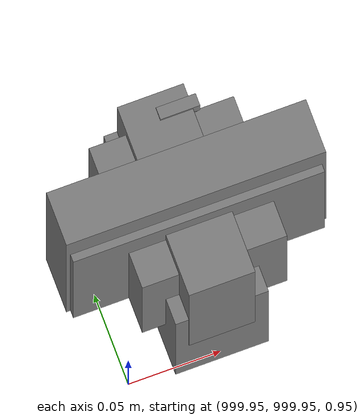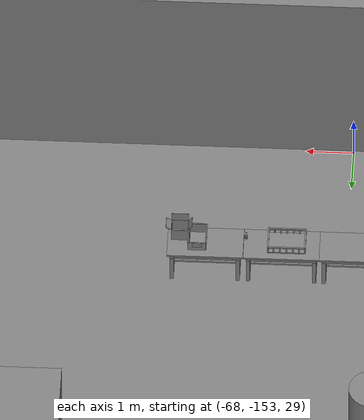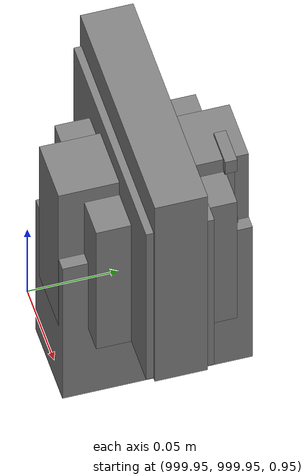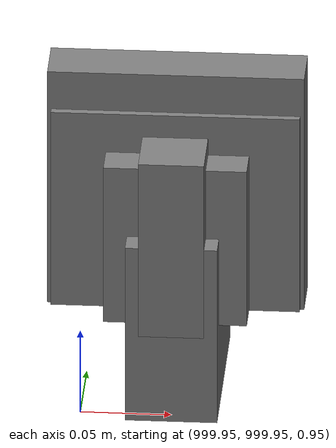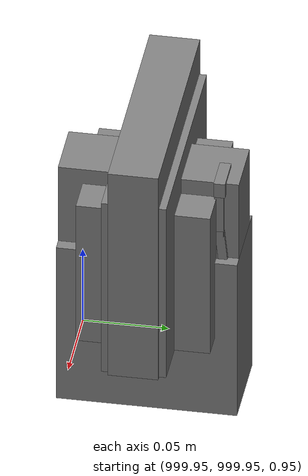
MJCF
<mujoco>
    <option gravity="0.000000000 0.000000000 -9.810000420" timestep="0.0049999999" integrator="implicitfast" density="1.225" viscosity="1.8000001e-05" noslip_iterations="10" iterations="100" sdf_iterations="50">
        <flag multiccd="disable"/>
    </option>
    <size memory="1000M"/>
    <compiler coordinate="local"/>
    <worldbody>
        <light cutoff="30" pos="0 1 1" dir="0 -1 -2"/>
        <light cutoff="30" pos="0 -1 1" dir="0 1 -2"/>
        <body pos="1000.000000000 1000.000000000 1.000000000" euler="0.000000000 0.000000000 180.000000000" name="openloong_gripper_2f85_fix_base_usda_battery_01">
            <geom contype="1" conaffinity="1" density="1000" type="box" material="" rgba="0.500000000 0.500000000 0.500000000 1.000000000" solimp="0.899999976 0.949999988 0.001000000" friction="1.000000000 0.005000000 0.000100000" solref="0.020000000 1.000000000" margin="0" condim="3" group="0" pos="-0.011123657 -0.041940309 0.101691343" quat="1.000000000 0.000000000 0.000000000 0.000000000" size="0.010800000 0.003375000 0.004725000" name="openloong_gripper_2f85_fix_base_usda_geom_1CC11CE7_51A7_4B04_A58B_56181E0DBD1C"/>
            <geom contype="1" conaffinity="1" density="1000" type="box" material="" rgba="0.500000000 0.500000000 0.500000000 1.000000000" solimp="0.899999976 0.949999988 0.001000000" friction="1.000000000 0.005000000 0.000100000" solref="0.020000000 1.000000000" margin="0" condim="3" group="0" pos="-0.010876465 -0.044247437 0.047066893" quat="0.998702705 -0.050920475 0.000000000 0.000000000" size="0.009450001 0.002700000 0.024975000" name="openloong_gripper_2f85_fix_base_usda_geom_6F8CC8E1_B1FF_4878_ADAA_2C95E97D8D1E"/>
            <geom contype="1" conaffinity="1" density="1000" type="box" material="" rgba="0.500000000 0.500000000 0.500000000 1.000000000" solimp="0.899999976 0.949999988 0.001000000" friction="1.000000000 0.005000000 0.000100000" solref="0.020000000 1.000000000" margin="0" condim="3" group="0" pos="-0.001235962 -0.000659180 0.047381196" quat="1.000000000 0.000000000 0.000000000 0.000000000" size="0.039420001 0.039150000 0.047250003" name="openloong_gripper_2f85_fix_base_usda_geom_278F09B5_6EEE_45C2_99ED_EB1C900B940B"/>
            <geom contype="1" conaffinity="1" density="1000" type="box" material="" rgba="0.500000000 0.500000000 0.500000000 1.000000000" solimp="0.899999976 0.949999988 0.001000000" friction="1.000000000 0.005000000 0.000100000" solref="0.020000000 1.000000000" margin="0" condim="3" group="0" pos="-0.010876465 -0.039138794 0.009851727" quat="1.000000000 0.000000000 0.000000000 0.000000000" size="0.009450001 0.010800000 0.013500000" name="openloong_gripper_2f85_fix_base_usda_geom_C4A6C904_DECF_4FC2_B42D_930310FBB56E"/>
            <geom contype="1" conaffinity="1" density="1000" type="box" material="" rgba="0.500000000 0.500000000 0.500000000 1.000000000" solimp="0.899999976 0.949999988 0.001000000" friction="1.000000000 0.005000000 0.000100000" solref="0.020000000 1.000000000" margin="0" condim="3" group="0" pos="-0.010876465 -0.041528322 0.071508206" quat="1.000000000 0.000000000 0.000000000 0.000000000" size="0.009450001 0.002700000 0.027000001" name="openloong_gripper_2f85_fix_base_usda_geom_F0EE7C01_59C7_4D10_A3E9_A4165F349E58"/>
            <freejoint name="openloong_gripper_2f85_fix_base_usda_battery_01_joint"/>
            <site size="0.005000000 0.005000000 0.005000000" rgba="0.500000000 0.500000000 0.500000000 1.000000000" pos="0.000000000 0.000000000 0.000000000" quat="0.999961913 0.008726500 0.000000000 0.000000000" group="0" type="sphere" name="openloong_gripper_2f85_fix_base_usda_battery_01site"/>
        </body>
        <body pos="1000.000000000 1000.000000000 1.000000000" euler="0.000000000 0.000000000 180.000000000" name="openloong_gripper_2f85_fix_base_usda_cpu_fan">
            <geom contype="1" conaffinity="1" density="1000" type="box" material="" rgba="0.500000000 0.500000000 0.500000000 1.000000000" solimp="0.899999976 0.949999988 0.001000000" friction="1.000000000 0.005000000 0.000100000" solref="0.020000000 1.000000000" margin="0" condim="3" group="0" pos="0.000000000 0.000000000 0.070034981" quat="0.000000000 0.000000000 0.000000000 1.000000000" size="0.070700005 0.014699999 0.070700005" name="openloong_gripper_2f85_fix_base_usda_geom_A4628567_01A8_4194_B715_920C24B739F0"/>
            <freejoint name="openloong_gripper_2f85_fix_base_usda_cpu_fan_joint"/>
            <site size="0.005000000 0.005000000 0.005000000" rgba="0.500000000 0.500000000 0.500000000 1.000000000" pos="0.000000000 0.000000000 0.000000000" quat="0.999961913 0.008726535 0.000000000 0.000000000" group="0" type="sphere" name="openloong_gripper_2f85_fix_base_usda_cpu_fancsite"/>
        </body>
        <body pos="1000.000000000 1000.000000000 1.000000000" euler="0.000000000 0.000000000 180.000000000" name="openloong_gripper_2f85_fix_base_usda_wifi_box">
            <geom contype="1" conaffinity="1" density="1000" type="box" material="" rgba="0.500000000 0.500000000 0.500000000 1.000000000" solimp="0.899999976 0.949999988 0.001000000" friction="1.000000000 0.005000000 0.000100000" solref="0.020000000 1.000000000" margin="0" condim="3" group="0" pos="0.000000000 0.000000000 0.058978677" quat="0.000000000 0.000000047 0.000000000 1.000000000" size="0.068499997 0.018999999 0.059000000" name="openloong_gripper_2f85_fix_base_usda_geom_EE3DA5C9_9A28_496D_8D36_6915A6DEFDCA"/>
            <freejoint name="openloong_gripper_2f85_fix_base_usda_wifi_box_joint"/>
            <site size="0.005000000 0.005000000 0.005000000" rgba="0.500000000 0.500000000 0.500000000 1.000000000" pos="0.000000000 0.000000000 0.000000000" quat="0.999961913 0.008726500 0.000000000 0.000000000" group="0" type="sphere" name="openloong_gripper_2f85_fix_base_usda_wifi_boxsite"/>
        </body>
        <body pos="-66.001785278 -149.502212524 31.167144775" euler="141.790527344 -51.682826996 145.938125610" mocap="true" name="spotlight6_SpotLight"/>
        <body pos="1000.000000000 1000.000000000 1.000000000" euler="0.000011953 0.000005123 -179.999984741" name="openloong_gripper_2f85_fix_base_usda_intel_box">
            <geom contype="1" conaffinity="1" density="1000" type="box" material="" rgba="0.500000000 0.500000000 0.500000000 1.000000000" solimp="0.899999976 0.949999988 0.001000000" friction="1.000000000 0.005000000 0.000100000" solref="0.020000000 1.000000000" margin="0" condim="3" group="0" pos="0.000000000 -0.000067139 0.000082284" quat="0.707106709 0.000000225 0.000000253 0.707106650" size="0.052800003 0.025300000 0.052800003" name="openloong_gripper_2f85_fix_base_usda_geom_24475DAD_487E_44F2_96C5_6A207DF9B3F8"/>
            <freejoint name="openloong_gripper_2f85_fix_base_usda_intel_box_joint"/>
            <site size="0.005000000 0.005000000 0.005000000" rgba="0.500000000 0.500000000 0.500000000 1.000000000" pos="0.000000000 0.000000000 0.000000000" quat="0.999961913 0.008726500 0.000000000 0.000000000" group="0" type="sphere" name="openloong_gripper_2f85_fix_base_usda_intel_boxsite"/>
        </body>
        <body pos="1000.000000000 999.999938965 1.000000000" euler="0.000000000 0.000000000 180.000000000" name="openloong_gripper_2f85_fix_base_usda_intelcore_i5">
            <geom contype="1" conaffinity="1" density="1000" type="box" material="" rgba="0.500000000 0.500000000 0.500000000 1.000000000" solimp="0.899999976 0.949999988 0.001000000" friction="1.000000000 0.005000000 0.000100000" solref="0.020000000 1.000000000" margin="0" condim="3" group="0" pos="0.000000000 0.000000000 0.051722717" quat="0.707106709 0.000000000 0.000000000 -0.707106769" size="0.052800000 0.018080002 0.052800000" name="openloong_gripper_2f85_fix_base_usda_geom_1C8016F9_09D1_4CF9_9AB4_2B4B052584CE"/>
            <freejoint name="openloong_gripper_2f85_fix_base_usda_intelcore_i5_joint"/>
            <site size="0.005000000 0.005000000 0.005000000" rgba="0.500000000 0.500000000 0.500000000 1.000000000" pos="0.000000000 0.000000000 0.000000000" quat="0.999961913 0.008726534 0.000000000 0.000000000" group="0" type="sphere" name="openloong_gripper_2f85_fix_base_usda_intelcore_i5site"/>
        </body>
        <body pos="-65.898117065 -149.549026489 31.165443420" euler="178.942459106 -48.370201111 173.119003296" mocap="true" name="spotlight2_SpotLight"/>
        <body pos="-66.395515442 -149.684051514 31.167579651" euler="7.411532402 -77.819992065 21.826074600" mocap="true" name="spotlight1_SpotLight"/>
        <body pos="-64.866622925 -149.383972168 30.183746338" euler="89.999984741 89.999946594 0.000000000" name="openloong_gripper_2f85_fix_base_usda_bluebox_01">
            <geom contype="1" conaffinity="1" density="1000" type="box" material="" rgba="0.500000000 0.500000000 0.500000000 1.000000000" solimp="0.899999976 0.949999988 0.001000000" friction="1.000000000 0.005000000 0.000100000" solref="0.020000000 1.000000000" margin="0" condim="3" group="0" pos="0.276580811 0.187225342 0.000068665" quat="0.707106948 0.000077471 0.707106352 0.000077486" size="0.100000001 0.057999998 0.010000000" name="openloong_gripper_2f85_fix_base_usda_geom_4D267CF5_5341_4C9D_A773_A81F68411979"/>
            <geom contype="1" conaffinity="1" density="1000" type="box" material="" rgba="0.500000000 0.500000000 0.500000000 1.000000000" solimp="0.899999976 0.949999988 0.001000000" friction="1.000000000 0.005000000 0.000100000" solref="0.020000000 1.000000000" margin="0" condim="3" group="0" pos="0.000000000 0.002883911 0.000000000" quat="0.999999881 0.000000000 0.000000000 0.000000000" size="0.254000008 0.003000000 0.172000006" name="openloong_gripper_2f85_fix_base_usda_geom_D87D114C_AA80_4186_94F9_FCF7817C59C7"/>
            <geom contype="1" conaffinity="1" density="1000" type="box" material="" rgba="0.500000000 0.500000000 0.500000000 1.000000000" solimp="0.899999976 0.949999988 0.001000000" friction="1.000000000 0.005000000 0.000100000" solref="0.020000000 1.000000000" margin="0" condim="3" group="0" pos="0.000000000 0.124874115 0.173484802" quat="0.999796331 0.020176515 -0.000000015 0.000000030" size="0.259999990 0.119999997 0.007000000" name="openloong_gripper_2f85_fix_base_usda_geom_1812E893_4F90_4525_8CBB_C69263BAC2EB"/>
            <geom contype="1" conaffinity="1" density="1000" type="box" material="" rgba="0.500000000 0.500000000 0.500000000 1.000000000" solimp="0.899999976 0.949999988 0.001000000" friction="1.000000000 0.005000000 0.000100000" solref="0.020000000 1.000000000" margin="0" condim="3" group="0" pos="0.000000000 0.124874115 -0.173469543" quat="0.999796331 -0.020176545 -0.000000015 0.000000000" size="0.259999990 0.119999997 0.007000000" name="openloong_gripper_2f85_fix_base_usda_geom_1C1E7563_5878_4288_90FC_8EDB74501613"/>
            <geom contype="1" conaffinity="1" density="1000" type="box" material="" rgba="0.500000000 0.500000000 0.500000000 1.000000000" solimp="0.899999976 0.949999988 0.001000000" friction="1.000000000 0.005000000 0.000100000" solref="0.020000000 1.000000000" margin="0" condim="3" group="0" pos="0.000000000 0.214008331 0.188980103" quat="0.999912977 0.013176724 0.000000015 0.000000000" size="0.259999990 0.029999999 0.012500000" name="openloong_gripper_2f85_fix_base_usda_geom_2FEEBDED_859D_4900_AECB_F3A5F272C4A3"/>
            <geom contype="1" conaffinity="1" density="1000" type="box" material="" rgba="0.500000000 0.500000000 0.500000000 1.000000000" solimp="0.899999976 0.949999988 0.001000000" friction="1.000000000 0.005000000 0.000100000" solref="0.020000000 1.000000000" margin="0" condim="3" group="0" pos="-0.258361816 0.125289917 0.001876831" quat="0.702796936 -0.020792112 0.710783124 0.020769298" size="0.189999998 0.119999997 0.009000000" name="openloong_gripper_2f85_fix_base_usda_geom_B6A569AD_CD8C_4151_8558_7D683E98DE03"/>
            <geom contype="1" conaffinity="1" density="1000" type="box" material="" rgba="0.500000000 0.500000000 0.500000000 1.000000000" solimp="0.899999976 0.949999988 0.001000000" friction="1.000000000 0.005000000 0.000100000" solref="0.020000000 1.000000000" margin="0" condim="3" group="0" pos="0.000000000 0.214008331 -0.188980103" quat="0.999912977 -0.013176769 0.000000030 0.000000015" size="0.259999990 0.029999999 0.012500000" name="openloong_gripper_2f85_fix_base_usda_geom_82AFAD03_7B52_478D_B5BA_EE8DA59A4F26"/>
            <geom contype="1" conaffinity="1" density="1000" type="box" material="" rgba="0.500000000 0.500000000 0.500000000 1.000000000" solimp="0.899999976 0.949999988 0.001000000" friction="1.000000000 0.005000000 0.000100000" solref="0.020000000 1.000000000" margin="0" condim="3" group="0" pos="-0.276611328 0.187225342 0.000068665" quat="0.707106650 0.000077441 0.707106709 0.000077456" size="0.100000001 0.057999998 0.010000000" name="openloong_gripper_2f85_fix_base_usda_geom_2ABDF51A_CDB2_490A_B2CE_C7A23738E031"/>
            <geom contype="1" conaffinity="1" density="1000" type="box" material="" rgba="0.500000000 0.500000000 0.500000000 1.000000000" solimp="0.899999976 0.949999988 0.001000000" friction="1.000000000 0.005000000 0.000100000" solref="0.020000000 1.000000000" margin="0" condim="3" group="0" pos="0.258331299 0.125289917 0.001876831" quat="0.702851415 0.018856421 0.710823774 -0.019329369" size="0.189999998 0.119999997 0.009000000" name="openloong_gripper_2f85_fix_base_usda_geom_5CF47FF9_5DAB_4DB0_8D13_9C278BD38E0D"/>
            <freejoint name="openloong_gripper_2f85_fix_base_usda_bluebox_01_joint"/>
            <site size="0.005000000 0.005000000 0.005000000" rgba="0.500000000 0.500000000 0.500000000 1.000000000" pos="0.000000000 0.000000000 0.000000000" quat="0.999961913 0.008726534 0.000000000 0.000000000" group="0" type="sphere" name="openloong_gripper_2f85_fix_base_usda_bluebox_01site"/>
        </body>
        <body pos="-64.496299744 -149.491867065 30.235729218" euler="0.000000000 0.000000000 89.999946594" name="openloong_gripper_2f85_fix_base_usda_cardboardbox_01">
            <geom contype="1" conaffinity="1" density="1000" type="box" material="" rgba="0.500000000 0.500000000 0.500000000 1.000000000" solimp="0.899999976 0.949999988 0.001000000" friction="1.000000000 0.005000000 0.000100000" solref="0.020000000 1.000000000" margin="0" condim="3" group="0" pos="-0.003166199 -0.004086494 0.005052090" quat="1.000000000 0.000000000 0.000000000 0.000000000" size="0.142499998 0.177500010 0.005000000" name="openloong_gripper_2f85_fix_base_usda_geom_4DC9B8B2_E43C_4CE6_87DF_FBD379E6C1DE"/>
            <geom contype="1" conaffinity="1" density="1000" type="box" material="" rgba="0.500000000 0.500000000 0.500000000 1.000000000" solimp="0.899999976 0.949999988 0.001000000" friction="1.000000000 0.005000000 0.000100000" solref="0.020000000 1.000000000" margin="0" condim="3" group="0" pos="-0.003166199 0.170316696 0.150570869" quat="1.000000000 0.000000000 0.000000000 0.000000000" size="0.142499998 0.005000000 0.149999991" name="openloong_gripper_2f85_fix_base_usda_geom_AD8F8246_24C5_4976_B37F_860077A90E69"/>
            <geom contype="1" conaffinity="1" density="1000" type="box" material="" rgba="0.500000000 0.500000000 0.500000000 1.000000000" solimp="0.899999976 0.949999988 0.001000000" friction="1.000000000 0.005000000 0.000100000" solref="0.020000000 1.000000000" margin="0" condim="3" group="0" pos="-0.147399902 -0.005307198 0.150570869" quat="1.000000000 0.000000000 0.000000000 0.000000000" size="0.005000000 0.177500010 0.149999991" name="openloong_gripper_2f85_fix_base_usda_geom_F224D610_7C14_4880_805F_C6DCA7E9AEFC"/>
            <geom contype="1" conaffinity="1" density="1000" type="box" material="" rgba="0.500000000 0.500000000 0.500000000 1.000000000" solimp="0.899999976 0.949999988 0.001000000" friction="1.000000000 0.005000000 0.000100000" solref="0.020000000 1.000000000" margin="0" condim="3" group="0" pos="0.140275955 -0.005307198 0.150570869" quat="1.000000000 0.000000000 0.000000000 0.000000000" size="0.005000000 0.177500010 0.149999991" name="openloong_gripper_2f85_fix_base_usda_geom_C09BF36E_DC85_4482_9221_BED1390C35D3"/>
            <geom contype="1" conaffinity="1" density="1000" type="box" material="" rgba="0.500000000 0.500000000 0.500000000 1.000000000" solimp="0.899999976 0.949999988 0.001000000" friction="1.000000000 0.005000000 0.000100000" solref="0.020000000 1.000000000" margin="0" condim="3" group="0" pos="-0.003166199 -0.181550980 0.150570869" quat="1.000000000 0.000000000 0.000000000 0.000000000" size="0.142499998 0.005000000 0.149999991" name="openloong_gripper_2f85_fix_base_usda_geom_29365A15_B824_4526_A1F2_97356B05524C"/>
            <freejoint name="openloong_gripper_2f85_fix_base_usda_cardboardbox_01_joint"/>
            <site size="0.005000000 0.005000000 0.005000000" rgba="0.500000000 0.500000000 0.500000000 1.000000000" pos="0.000000000 0.000000000 0.000000000" quat="0.999961913 0.008726535 0.000000000 0.000000000" group="0" type="sphere" name="openloong_gripper_2f85_fix_base_usda_site_A849820E_4216_4AE2_8756_3BF6C87ED8D0"/>
            <body pos="0.139160156 -0.004048347 0.301930904" euler="-179.999954224 49.383502960 179.999954224" name="openloong_gripper_2f85_fix_base_usda_A1_006">
                <geom contype="1" conaffinity="1" density="1000" type="box" material="" rgba="0.500000000 0.500000000 0.500000000 1.000000000" solimp="0.899999976 0.949999988 0.001000000" friction="1.000000000 0.005000000 0.000100000" solref="0.020000000 1.000000000" margin="0" condim="3" group="0" pos="-0.071587563 0.000009537 0.001745224" quat="0.999999881 0.000000000 0.000000000 0.000000000" size="0.071249999 0.179999992 0.002500000" name="openloong_gripper_2f85_fix_base_usda_geom_868CAE0A_931D_4FCE_BF1A_F24850A229D1"/>
                <joint armature="0" stiffness="0.07" damping="0.0099999998" axis="0.000000 1.000000 0.000000" type="hinge" name="openloong_gripper_2f85_fix_base_usda_A1_006"/>
            </body>
            <body pos="-0.145902634 -0.004086494 0.301938057" euler="-180.000000000 -60.000011444 -180.000000000" name="openloong_gripper_2f85_fix_base_usda_A2_006">
                <geom contype="1" conaffinity="1" density="1000" type="box" material="" rgba="0.500000000 0.500000000 0.500000000 1.000000000" solimp="0.899999976 0.949999988 0.001000000" friction="1.000000000 0.005000000 0.000100000" solref="0.020000000 1.000000000" margin="0" condim="3" group="0" pos="0.071268082 0.000009537 0.002717972" quat="0.000002921 0.000000000 -0.000000030 0.999999881" size="0.071249999 0.179999992 0.002500000" name="openloong_gripper_2f85_fix_base_usda_geom_E34D1A99_E515_4E37_8380_FAD00CE405CB"/>
                <joint armature="0" stiffness="0.07" damping="0.0099999998" axis="0.000000 1.000000 0.000000" type="hinge" name="openloong_gripper_2f85_fix_base_usda_A2_006"/>
            </body>
            <body pos="-0.003385544 0.175991058 0.301930904" euler="-125.858116150 -0.000004561 0.000002331" name="openloong_gripper_2f85_fix_base_usda_B2_006">
                <geom contype="1" conaffinity="1" density="1000" type="box" material="" rgba="0.500000000 0.500000000 0.500000000 1.000000000" solimp="0.899999976 0.949999988 0.001000000" friction="1.000000000 0.005000000 0.000100000" solref="0.020000000 1.000000000" margin="0" condim="3" group="0" pos="0.000009537 -0.070939064 -0.002470016" quat="0.999614120 0.027776197 -0.000000015 0.000000030" size="0.137500003 0.064999998 0.005000000" name="openloong_gripper_2f85_fix_base_usda_geom_AEE38DAA_5C74_488B_9FFF_820FF3AE6364"/>
                <joint armature="0" stiffness="0.07" damping="0.0099999998" axis="1.000000 0.000000 0.000000" type="hinge" name="openloong_gripper_2f85_fix_base_usda_B2_006"/>
            </body>
            <body pos="-0.003385544 -0.184140205 0.301938057" euler="147.805557251 0.000000000 0.000000000" name="openloong_gripper_2f85_fix_base_usda_B1_006">
                <geom contype="1" conaffinity="1" density="1000" type="box" material="" rgba="0.500000000 0.500000000 0.500000000 1.000000000" solimp="0.899999976 0.949999988 0.001000000" friction="1.000000000 0.005000000 0.000100000" solref="0.020000000 1.000000000" margin="0" condim="3" group="0" pos="-0.000028610 0.070202351 -0.002703667" quat="0.999614179 -0.027776167 0.000000000 0.000000000" size="0.137500003 0.064999998 0.005000000" name="openloong_gripper_2f85_fix_base_usda_geom_6DC67F37_EED3_4935_AAEA_957B9CF693C4"/>
                <joint armature="0" stiffness="0.07" damping="0.0099999998" axis="1.000000 0.000000 0.000000" type="hinge" name="openloong_gripper_2f85_fix_base_usda_B1_006"/>
            </body>
        </body>
        <body pos="-65.882858276 -149.481979370 30.229999542" euler="-64.487716675 0.000000000 0.000000000" name="openloong_gripper_2f85_fix_base_usda_Barcode">
            <geom contype="1" conaffinity="1" density="1000" type="box" material="" rgba="0.500000000 0.500000000 0.500000000 1.000000000" solimp="0.899999976 0.949999988 0.001000000" friction="1.000000000 0.005000000 0.000100000" solref="0.020000000 1.000000000" margin="0" condim="3" group="0" pos="0.000000000 0.013038635 0.001419067" quat="0.000000000 0.000000000 0.000000000 1.000000119" size="0.034000002 0.010000000 0.017999999" name="openloong_gripper_2f85_fix_base_usda_geom_68F78FC1_E4F2_4016_853B_33C432AD4ED3"/>
            <geom contype="1" conaffinity="1" density="1000" type="box" material="" rgba="0.500000000 0.500000000 0.500000000 1.000000000" solimp="0.899999976 0.949999988 0.001000000" friction="1.000000000 0.005000000 0.000100000" solref="0.020000000 1.000000000" margin="0" condim="3" group="0" pos="0.000000000 -0.035301208 -0.007095337" quat="0.000000000 0.000000000 -0.043619365 0.999048233" size="0.028999999 0.010000000 0.020000000" name="openloong_gripper_2f85_fix_base_usda_geom_10743E93_AB35_45B5_B0DA_C5AB16779118"/>
            <geom contype="1" conaffinity="1" density="1000" type="box" material="" rgba="0.500000000 0.500000000 0.500000000 1.000000000" solimp="0.899999976 0.949999988 0.001000000" friction="1.000000000 0.005000000 0.000100000" solref="0.020000000 1.000000000" margin="0" condim="3" group="0" pos="0.000000000 -0.043411255 -0.011749268" quat="0.922262907 0.386563420 0.000000000 0.000000000" size="0.026000001 0.010000000 0.020000000" name="openloong_gripper_2f85_fix_base_usda_geom_56AFA071_C5D5_4676_AEB5_701178EC70CD"/>
            <geom contype="1" conaffinity="1" density="1000" type="box" material="" rgba="0.500000000 0.500000000 0.500000000 1.000000000" solimp="0.899999976 0.949999988 0.001000000" friction="1.000000000 0.005000000 0.000100000" solref="0.020000000 1.000000000" margin="0" condim="3" group="0" pos="0.000000000 -0.016967773 -0.031860352" quat="0.000000000 0.000000000 0.000000000 1.000000119" size="0.008000000 0.010000000 0.013000000" name="openloong_gripper_2f85_fix_base_usda_geom_B68346B8_D182_4150_BB5F_855473663B93"/>
            <geom contype="1" conaffinity="1" density="1000" type="box" material="" rgba="0.500000000 0.500000000 0.500000000 1.000000000" solimp="0.899999976 0.949999988 0.001000000" friction="1.000000000 0.005000000 0.000100000" solref="0.020000000 1.000000000" margin="0" condim="3" group="0" pos="0.000000000 -0.001869202 0.000312805" quat="0.953716993 0.300705761 0.000000000 0.000000000" size="0.032000002 0.010000000 0.018999999" name="openloong_gripper_2f85_fix_base_usda_geom_A6894C63_BE3D_4E9A_9D2A_87EF5C0E0F9E"/>
            <geom contype="1" conaffinity="1" density="1000" type="box" material="" rgba="0.500000000 0.500000000 0.500000000 1.000000000" solimp="0.899999976 0.949999988 0.001000000" friction="1.000000000 0.005000000 0.000100000" solref="0.020000000 1.000000000" margin="0" condim="3" group="0" pos="0.000000000 -0.019531250 -0.003173828" quat="0.953716993 0.300705761 0.000000000 0.000000000" size="0.030999999 0.010000000 0.020000000" name="openloong_gripper_2f85_fix_base_usda_geom_91C2E5B9_4B0D_4E93_BBFB_992748173E21"/>
            <geom contype="1" conaffinity="1" density="1000" type="box" material="" rgba="0.500000000 0.500000000 0.500000000 1.000000000" solimp="0.899999976 0.949999988 0.001000000" friction="1.000000000 0.005000000 0.000100000" solref="0.020000000 1.000000000" margin="0" condim="3" group="0" pos="0.000000000 -0.035301208 -0.007095337" quat="0.953716993 0.300705761 0.000000000 0.000000000" size="0.028999999 0.010000000 0.020000000" name="openloong_gripper_2f85_fix_base_usda_geom_0C80A55C_328D_4743_A839_EAB9F003A5D7"/>
            <geom contype="1" conaffinity="1" density="1000" type="box" material="" rgba="0.500000000 0.500000000 0.500000000 1.000000000" solimp="0.899999976 0.949999988 0.001000000" friction="1.000000000 0.005000000 0.000100000" solref="0.020000000 1.000000000" margin="0" condim="3" group="0" pos="0.000000000 -0.042617798 -0.071121216" quat="0.000000000 0.000000000 0.000000000 1.000000119" size="0.013000000 0.021000000 0.059999999" name="openloong_gripper_2f85_fix_base_usda_geom_F5FBD60E_9773_4906_903F_851E34E583FC"/>
            <freejoint name="openloong_gripper_2f85_fix_base_usda_Barcode_joint"/>
            <site size="0.005000000 0.005000000 0.005000000" rgba="0.500000000 0.500000000 0.500000000 1.000000000" pos="0.000000000 0.000000000 0.000000000" quat="1.000000000 0.000000000 0.000000000 0.000000000" group="0" type="sphere" name="openloong_gripper_2f85_fix_base_usda_Barcode_site"/>
        </body>
        <body pos="-66.745018005 -149.392349243 30.184000015" euler="0.000000000 0.000000000 89.999946594" name="[22330482584601]_Basket_01">
            <geom contype="1" conaffinity="1" density="1000" type="box" material="" rgba="0.500000000 0.500000000 0.500000000 1.000000000" solimp="0.899999976 0.949999988 0.001000000" friction="1.000000000 0.005000000 0.000100000" solref="0.020000000 1.000000000" margin="0" condim="3" group="0" pos="-0.052425385 0.389207840 0.089787483" quat="0.707107008 0.000000000 0.000000000 0.707106411" size="0.014249999 0.014249999 0.059999999" name="[22330482584601]_geom_3190642D_D837_4E18_8FCD_0B0F9574F29B"/>
            <geom contype="1" conaffinity="1" density="1000" type="box" material="" rgba="0.500000000 0.500000000 0.500000000 1.000000000" solimp="0.899999976 0.949999988 0.001000000" friction="1.000000000 0.005000000 0.000100000" solref="0.020000000 1.000000000" margin="0" condim="3" group="0" pos="0.264015198 -0.133043289 0.089787483" quat="0.707107008 0.000000000 0.000000000 0.707106411" size="0.014249999 0.014249999 0.059999999" name="[22330482584601]_geom_680E16F0_40D4_44B0_889C_174FED4C4C80"/>
            <geom contype="1" conaffinity="1" density="1000" type="box" material="" rgba="0.500000000 0.500000000 0.500000000 1.000000000" solimp="0.899999976 0.949999988 0.001000000" friction="1.000000000 0.005000000 0.000100000" solref="0.020000000 1.000000000" margin="0" condim="3" group="0" pos="-0.264015198 -0.265548706 0.089793205" quat="0.707107008 0.000000000 0.000000000 0.707106411" size="0.014249999 0.014249999 0.059999999" name="[22330482584601]_geom_DFECD83A_4C39_4F63_8AAF_B352396C9774"/>
            <geom contype="1" conaffinity="1" density="1000" type="box" material="" rgba="0.500000000 0.500000000 0.500000000 1.000000000" solimp="0.899999976 0.949999988 0.001000000" friction="1.000000000 0.005000000 0.000100000" solref="0.020000000 1.000000000" margin="0" condim="3" group="0" pos="-0.160263062 -0.389322281 0.089793205" quat="0.707107008 0.000000000 0.000000000 0.707106411" size="0.014249999 0.014249999 0.059999999" name="[22330482584601]_geom_4FA198F0_B30D_46F9_AC00_82FC923FBFCC"/>
            <geom contype="1" conaffinity="1" density="1000" type="box" material="" rgba="0.500000000 0.500000000 0.500000000 1.000000000" solimp="0.899999976 0.949999988 0.001000000" friction="1.000000000 0.005000000 0.000100000" solref="0.020000000 1.000000000" margin="0" condim="3" group="0" pos="0.162265778 -0.389322281 0.089787483" quat="0.707107008 0.000000000 0.000000000 0.707106411" size="0.014249999 0.014249999 0.059999999" name="[22330482584601]_geom_7A0EF34F_3489_4671_81F2_E3981210A0E6"/>
            <geom contype="1" conaffinity="1" density="1000" type="box" material="" rgba="0.500000000 0.500000000 0.500000000 1.000000000" solimp="0.899999976 0.949999988 0.001000000" friction="1.000000000 0.005000000 0.000100000" solref="0.020000000 1.000000000" margin="0" condim="3" group="0" pos="0.264015198 0.389207840 0.089787483" quat="0.707107008 0.000000000 0.000000000 0.707106411" size="0.014249999 0.014249999 0.059999999" name="[22330482584601]_geom_224E5892_BF65_4BE5_B63D_2AF9B29682DC"/>
            <geom contype="1" conaffinity="1" density="1000" type="box" material="" rgba="0.500000000 0.500000000 0.500000000 1.000000000" solimp="0.899999976 0.949999988 0.001000000" friction="1.000000000 0.005000000 0.000100000" solref="0.020000000 1.000000000" margin="0" condim="3" group="0" pos="-0.264015198 -0.133043289 0.089793205" quat="0.707107008 0.000000000 0.000000000 0.707106411" size="0.014249999 0.014249999 0.059999999" name="[22330482584601]_geom_5863FA0F_117E_4ADC_916F_4BEA275F5F3F"/>
            <geom contype="1" conaffinity="1" density="1000" type="box" material="" rgba="0.500000000 0.500000000 0.500000000 1.000000000" solimp="0.899999976 0.949999988 0.001000000" friction="1.000000000 0.005000000 0.000100000" solref="0.020000000 1.000000000" margin="0" condim="3" group="0" pos="-0.264026642 0.269256592 0.089793205" quat="0.707107008 0.000000000 0.000000000 0.707106411" size="0.014249999 0.014249999 0.059999999" name="[22330482584601]_geom_2AB5357A_CD6B_4C75_A919_BE65A014194A"/>
            <geom contype="1" conaffinity="1" density="1000" type="box" material="" rgba="0.500000000 0.500000000 0.500000000 1.000000000" solimp="0.899999976 0.949999988 0.001000000" friction="1.000000000 0.005000000 0.000100000" solref="0.020000000 1.000000000" margin="0" condim="3" group="0" pos="0.054462433 0.389207840 0.089787483" quat="0.707107008 0.000000000 0.000000000 0.707106411" size="0.014249999 0.014249999 0.059999999" name="[22330482584601]_geom_E4476FE6_7474_4A2E_84C3_C6BBAA4B5348"/>
            <geom contype="1" conaffinity="1" density="1000" type="box" material="" rgba="0.500000000 0.500000000 0.500000000 1.000000000" solimp="0.899999976 0.949999988 0.001000000" friction="1.000000000 0.005000000 0.000100000" solref="0.020000000 1.000000000" margin="0" condim="3" group="0" pos="0.054462433 -0.389322281 0.089787483" quat="0.707107008 0.000000000 0.000000000 0.707106411" size="0.014249999 0.014249999 0.059999999" name="[22330482584601]_geom_01B67B96_B3CA_4639_83CF_6CB9612BDD63"/>
            <geom contype="1" conaffinity="1" density="1000" type="box" material="" rgba="0.500000000 0.500000000 0.500000000 1.000000000" solimp="0.899999976 0.949999988 0.001000000" friction="1.000000000 0.005000000 0.000100000" solref="0.020000000 1.000000000" margin="0" condim="3" group="0" pos="0.264015198 0.269256592 0.089793205" quat="0.707107008 0.000000000 0.000000000 0.707106411" size="0.014249999 0.014249999 0.059999999" name="[22330482584601]_geom_C6AEB1AE_EAC4_4EE7_84DB_DF1033E98E42"/>
            <geom contype="1" conaffinity="1" density="1000" type="box" material="" rgba="0.500000000 0.500000000 0.500000000 1.000000000" solimp="0.899999976 0.949999988 0.001000000" friction="1.000000000 0.005000000 0.000100000" solref="0.020000000 1.000000000" margin="0" condim="3" group="0" pos="0.264015198 -0.389322281 0.089787483" quat="0.707107008 0.000000000 0.000000000 0.707106411" size="0.014249999 0.014249999 0.059999999" name="[22330482584601]_geom_FAC236BF_526E_40E8_BDF9_4F9BF33CB353"/>
            <geom contype="1" conaffinity="1" density="1000" type="box" material="" rgba="0.500000000 0.500000000 0.500000000 1.000000000" solimp="0.899999976 0.949999988 0.001000000" friction="1.000000000 0.005000000 0.000100000" solref="0.020000000 1.000000000" margin="0" condim="3" group="0" pos="0.000000000 0.000000000 0.015998840" quat="0.707107008 0.000000000 0.000000000 0.707106411" size="0.403499991 0.279000014 0.015750000" name="[22330482584601]_geom_E32C259C_CEF8_4FB2_BEC5_A4954E9894CF"/>
            <geom contype="1" conaffinity="1" density="1000" type="box" material="" rgba="0.500000000 0.500000000 0.500000000 1.000000000" solimp="0.899999976 0.949999988 0.001000000" friction="1.000000000 0.005000000 0.000100000" solref="0.020000000 1.000000000" margin="0" condim="3" group="0" pos="0.000000000 -0.389476776 0.163619041" quat="0.707107008 0.000000000 0.000000000 0.707106411" size="0.015000000 0.277500004 0.015750000" name="[22330482584601]_geom_688DB701_2D01_4B7D_AF25_FF49D5313951"/>
            <geom contype="1" conaffinity="1" density="1000" type="box" material="" rgba="0.500000000 0.500000000 0.500000000 1.000000000" solimp="0.899999976 0.949999988 0.001000000" friction="1.000000000 0.005000000 0.000100000" solref="0.020000000 1.000000000" margin="0" condim="3" group="0" pos="0.162265778 0.389207840 0.089787483" quat="0.707107008 0.000000000 0.000000000 0.707106411" size="0.014249999 0.014249999 0.059999999" name="[22330482584601]_geom_B3F28B61_14B2_4563_B11D_BB732EB0F2FF"/>
            <geom contype="1" conaffinity="1" density="1000" type="box" material="" rgba="0.500000000 0.500000000 0.500000000 1.000000000" solimp="0.899999976 0.949999988 0.001000000" friction="1.000000000 0.005000000 0.000100000" solref="0.020000000 1.000000000" margin="0" condim="3" group="0" pos="0.000000000 0.389471054 0.163619041" quat="0.707107008 0.000000000 0.000000000 0.707106411" size="0.015000000 0.277500004 0.015750000" name="[22330482584601]_geom_CF8858E0_D884_46B7_9C3E_3DC3D4D1979A"/>
            <geom contype="1" conaffinity="1" density="1000" type="box" material="" rgba="0.500000000 0.500000000 0.500000000 1.000000000" solimp="0.899999976 0.949999988 0.001000000" friction="1.000000000 0.005000000 0.000100000" solref="0.020000000 1.000000000" margin="0" condim="3" group="0" pos="-0.263511658 0.000000000 0.163619041" quat="0.707107008 0.000000000 0.000000000 0.707106411" size="0.403499991 0.015000000 0.015750000" name="[22330482584601]_geom_0D05D8F2_2ED0_45F6_BC18_F4EDCF55E029"/>
            <geom contype="1" conaffinity="1" density="1000" type="box" material="" rgba="0.500000000 0.500000000 0.500000000 1.000000000" solimp="0.899999976 0.949999988 0.001000000" friction="1.000000000 0.005000000 0.000100000" solref="0.020000000 1.000000000" margin="0" condim="3" group="0" pos="-0.264015198 0.141334534 0.089793205" quat="0.707107008 0.000000000 0.000000000 0.707106411" size="0.014249999 0.014249999 0.059999999" name="[22330482584601]_geom_F6A749AB_8836_46D7_AC0F_6710444DBE92"/>
            <geom contype="1" conaffinity="1" density="1000" type="box" material="" rgba="0.500000000 0.500000000 0.500000000 1.000000000" solimp="0.899999976 0.949999988 0.001000000" friction="1.000000000 0.005000000 0.000100000" solref="0.020000000 1.000000000" margin="0" condim="3" group="0" pos="0.264015198 -0.265548706 0.089787483" quat="0.707107008 0.000000000 0.000000000 0.707106411" size="0.014249999 0.014249999 0.059999999" name="[22330482584601]_geom_C2298062_0B4B_4147_BA7D_21E9D7646B9C"/>
            <geom contype="1" conaffinity="1" density="1000" type="box" material="" rgba="0.500000000 0.500000000 0.500000000 1.000000000" solimp="0.899999976 0.949999988 0.001000000" friction="1.000000000 0.005000000 0.000100000" solref="0.020000000 1.000000000" margin="0" condim="3" group="0" pos="-0.160263062 0.389207840 0.089787483" quat="0.707107008 0.000000000 0.000000000 0.707106411" size="0.014249999 0.014249999 0.059999999" name="[22330482584601]_geom_0C7637E1_DF9E_475C_AC9F_425EC2D73B10"/>
            <geom contype="1" conaffinity="1" density="1000" type="box" material="" rgba="0.500000000 0.500000000 0.500000000 1.000000000" solimp="0.899999976 0.949999988 0.001000000" friction="1.000000000 0.005000000 0.000100000" solref="0.020000000 1.000000000" margin="0" condim="3" group="0" pos="-0.052425385 -0.389322281 0.089787483" quat="0.707107008 0.000000000 0.000000000 0.707106411" size="0.014249999 0.014249999 0.059999999" name="[22330482584601]_geom_2FC070CC_C068_422C_BE3A_90D226E55E02"/>
            <geom contype="1" conaffinity="1" density="1000" type="box" material="" rgba="0.500000000 0.500000000 0.500000000 1.000000000" solimp="0.899999976 0.949999988 0.001000000" friction="1.000000000 0.005000000 0.000100000" solref="0.020000000 1.000000000" margin="0" condim="3" group="0" pos="-0.264026642 -0.389322281 0.089793205" quat="0.707107008 0.000000000 0.000000000 0.707106411" size="0.014249999 0.014249999 0.059999999" name="[22330482584601]_geom_AE41C712_C168_4EEA_B0DA_6F214140D3F5"/>
            <geom contype="1" conaffinity="1" density="1000" type="box" material="" rgba="0.500000000 0.500000000 0.500000000 1.000000000" solimp="0.899999976 0.949999988 0.001000000" friction="1.000000000 0.005000000 0.000100000" solref="0.020000000 1.000000000" margin="0" condim="3" group="0" pos="0.264015198 0.141334534 0.089787483" quat="0.707107008 0.000000000 0.000000000 0.707106411" size="0.014249999 0.014249999 0.059999999" name="[22330482584601]_geom_23535938_3FBD_4B4F_B8A3_9A06015D8F88"/>
            <geom contype="1" conaffinity="1" density="1000" type="box" material="" rgba="0.500000000 0.500000000 0.500000000 1.000000000" solimp="0.899999976 0.949999988 0.001000000" friction="1.000000000 0.005000000 0.000100000" solref="0.020000000 1.000000000" margin="0" condim="3" group="0" pos="-0.264015198 0.389207840 0.089793205" quat="0.707107008 0.000000000 0.000000000 0.707106411" size="0.014249999 0.014249999 0.059999999" name="[22330482584601]_geom_D7663EAB_FC59_4A59_96E5_1CA540CD9EEA"/>
            <geom contype="1" conaffinity="1" density="1000" type="box" material="" rgba="0.500000000 0.500000000 0.500000000 1.000000000" solimp="0.899999976 0.949999988 0.001000000" friction="1.000000000 0.005000000 0.000100000" solref="0.020000000 1.000000000" margin="0" condim="3" group="0" pos="0.264015198 0.004480362 0.089787483" quat="0.707107008 0.000000000 0.000000000 0.707106411" size="0.014249999 0.014249999 0.059999999" name="[22330482584601]_geom_3EC1CABB_A9AA_4536_8CD5_A939CC6E7FF2"/>
            <geom contype="1" conaffinity="1" density="1000" type="box" material="" rgba="0.500000000 0.500000000 0.500000000 1.000000000" solimp="0.899999976 0.949999988 0.001000000" friction="1.000000000 0.005000000 0.000100000" solref="0.020000000 1.000000000" margin="0" condim="3" group="0" pos="0.263694763 -0.000011444 0.163619041" quat="0.707107008 0.000000000 0.000000000 0.707106411" size="0.403499991 0.015000000 0.015750000" name="[22330482584601]_geom_8CCBC279_7D88_4AF6_A457_5320056A326D"/>
            <geom contype="1" conaffinity="1" density="1000" type="box" material="" rgba="0.500000000 0.500000000 0.500000000 1.000000000" solimp="0.899999976 0.949999988 0.001000000" friction="1.000000000 0.005000000 0.000100000" solref="0.020000000 1.000000000" margin="0" condim="3" group="0" pos="-0.264015198 0.004480362 0.089793205" quat="0.707107008 0.000000000 0.000000000 0.707106411" size="0.014249999 0.014249999 0.059999999" name="[22330482584601]_geom_87FF746C_FDE5_49BF_B956_2A955481123A"/>
            <freejoint name="[22330482584601]_joint_1CCD02BF_52FC_4AA1_8665_1A24CB7FFF7F"/>
        </body>
        <body pos="0.000000000 0.000000000 0.000000000" euler="0.000000000 0.000000000 0.000000000" name="Static Objects_Static Objects">
            <geom contype="1" conaffinity="1" density="1000" type="box" material="" rgba="0.500000000 0.500000000 0.500000000 1.000000000" solimp="0.899999976 0.949999988 0.001000000" friction="1.000000000 0.005000000 0.000100000" solref="0.020000000 1.000000000" margin="0" condim="3" group="0" pos="-67.544113159 -149.365814209 29.727830887" quat="0.500000417 0.499999970 0.499999553 0.499999970" size="0.381000012 0.319999993 0.041000001" name="Static Objects_geom_831BA9D0_8D0A_4BBF_A20E_CEFAD742E100"/>
            <geom contype="1" conaffinity="1" density="1000" type="box" material="" rgba="0.500000000 0.500000000 0.500000000 1.000000000" solimp="0.899999976 0.949999988 0.001000000" friction="1.000000000 0.005000000 0.000100000" solref="0.020000000 1.000000000" margin="0" condim="3" group="0" pos="-68.239501953 -149.365814209 30.086868286" quat="0.500000417 0.499999970 0.499999553 0.499999970" size="0.370999992 0.039500002 0.745000005" name="Static Objects_geom_73D633E5_6A18_4247_8361_F502D82C8098"/>
            <geom contype="1" conaffinity="1" density="1000" type="box" material="" rgba="0.500000000 0.500000000 0.500000000 1.000000000" solimp="0.899999976 0.949999988 0.001000000" friction="1.000000000 0.005000000 0.000100000" solref="0.020000000 1.000000000" margin="0" condim="3" group="0" pos="-68.239501953 -149.365814209 30.147235870" quat="0.500000417 0.499999970 0.499999553 0.499999970" size="0.400000006 0.022000000 0.800000012" name="Static Objects_geom_818B505E_7EBC_4620_B15B_64B727D06757"/>
            <geom contype="1" conaffinity="1" density="1000" type="box" material="" rgba="0.500000000 0.500000000 0.500000000 1.000000000" solimp="0.899999976 0.949999988 0.001000000" friction="1.000000000 0.005000000 0.000100000" solref="0.020000000 1.000000000" margin="0" condim="3" group="0" pos="-68.934890747 -149.365814209 29.727830887" quat="0.500000417 0.499999970 0.499999553 0.499999970" size="0.381000012 0.319999993 0.041000001" name="Static Objects_geom_1ED5A50B_64EB_474E_A61C_143A0FF9F3FA"/>
            <geom contype="1" conaffinity="1" density="1000" type="box" material="" rgba="0.500000000 0.500000000 0.500000000 1.000000000" solimp="0.899999976 0.949999988 0.001000000" friction="1.000000000 0.005000000 0.000100000" solref="0.020000000 1.000000000" margin="0" condim="3" group="0" pos="-68.239501953 -149.365814209 29.561563492" quat="0.500000417 0.499999970 0.499999553 0.499999970" size="0.020000000 0.022000000 0.660000026" name="Static Objects_geom_6E4560EE_1772_4FDE_AA71_C9E3736C519D"/>
            <geom contype="1" conaffinity="1" density="1000" type="box" material="" rgba="0.500000000 0.500000000 0.500000000 1.000000000" solimp="0.899999976 0.949999988 0.001000000" friction="1.000000000 0.005000000 0.000100000" solref="0.020000000 1.000000000" margin="0" condim="3" group="0" pos="-65.945671082 -149.365814209 29.727830887" quat="0.500000417 0.499999970 0.499999553 0.499999970" size="0.381000012 0.319999993 0.041000001" name="Static Objects_geom_B91BAAC7_4D58_4119_94CA_E59DB938E96A"/>
            <geom contype="1" conaffinity="1" density="1000" type="box" material="" rgba="0.500000000 0.500000000 0.500000000 1.000000000" solimp="0.899999976 0.949999988 0.001000000" friction="1.000000000 0.005000000 0.000100000" solref="0.020000000 1.000000000" margin="0" condim="3" group="0" pos="-66.641059875 -149.365814209 30.086868286" quat="0.500000417 0.499999970 0.499999553 0.499999970" size="0.370999992 0.039500002 0.745000005" name="Static Objects_geom_7E8A2AC6_121F_4CE4_82F1_FCF0BB7AF1A3"/>
            <geom contype="1" conaffinity="1" density="1000" type="box" material="" rgba="0.500000000 0.500000000 0.500000000 1.000000000" solimp="0.899999976 0.949999988 0.001000000" friction="1.000000000 0.005000000 0.000100000" solref="0.020000000 1.000000000" margin="0" condim="3" group="0" pos="-66.641059875 -149.365814209 30.147235870" quat="0.500000417 0.499999970 0.499999553 0.499999970" size="0.400000006 0.022000000 0.800000012" name="Static Objects_geom_ADC7E713_6718_4F8A_9584_5D40251A858A"/>
            <geom contype="1" conaffinity="1" density="1000" type="box" material="" rgba="0.500000000 0.500000000 0.500000000 1.000000000" solimp="0.899999976 0.949999988 0.001000000" friction="1.000000000 0.005000000 0.000100000" solref="0.020000000 1.000000000" margin="0" condim="3" group="0" pos="-67.336448669 -149.365814209 29.727830887" quat="0.500000417 0.499999970 0.499999553 0.499999970" size="0.381000012 0.319999993 0.041000001" name="Static Objects_geom_6D48AD7A_D805_4715_8E88_27C2E43C7225"/>
            <geom contype="1" conaffinity="1" density="1000" type="box" material="" rgba="0.500000000 0.500000000 0.500000000 1.000000000" solimp="0.899999976 0.949999988 0.001000000" friction="1.000000000 0.005000000 0.000100000" solref="0.020000000 1.000000000" margin="0" condim="3" group="0" pos="-66.641059875 -149.365814209 29.561563492" quat="0.500000417 0.499999970 0.499999553 0.499999970" size="0.020000000 0.022000000 0.660000026" name="Static Objects_geom_3F32809E_3EF9_496A_AFD2_947E65CFD703"/>
            <geom contype="1" conaffinity="1" density="1000" type="box" material="" rgba="0.500000000 0.500000000 0.500000000 1.000000000" solimp="0.899999976 0.949999988 0.001000000" friction="1.000000000 0.005000000 0.000100000" solref="0.020000000 1.000000000" margin="0" condim="3" group="0" pos="-64.338577271 -149.365814209 29.727830887" quat="0.500000417 0.499999970 0.499999553 0.499999970" size="0.381000012 0.319999993 0.041000001" name="Static Objects_geom_BCDB92EB_9D00_4BBE_833A_01757005792A"/>
            <geom contype="1" conaffinity="1" density="1000" type="box" material="" rgba="0.500000000 0.500000000 0.500000000 1.000000000" solimp="0.899999976 0.949999988 0.001000000" friction="1.000000000 0.005000000 0.000100000" solref="0.020000000 1.000000000" margin="0" condim="3" group="0" pos="-65.033966064 -149.365814209 30.086868286" quat="0.500000417 0.499999970 0.499999553 0.499999970" size="0.370999992 0.039500002 0.745000005" name="Static Objects_geom_B2632186_C654_49C0_A103_AC8B27509986"/>
            <geom contype="1" conaffinity="1" density="1000" type="box" material="" rgba="0.500000000 0.500000000 0.500000000 1.000000000" solimp="0.899999976 0.949999988 0.001000000" friction="1.000000000 0.005000000 0.000100000" solref="0.020000000 1.000000000" margin="0" condim="3" group="0" pos="-65.033966064 -149.365814209 30.147235870" quat="0.500000417 0.499999970 0.499999553 0.499999970" size="0.400000006 0.022000000 0.800000012" name="Static Objects_geom_AF41BC19_83B2_4C12_8519_3DDC10379234"/>
            <geom contype="1" conaffinity="1" density="1000" type="box" material="" rgba="0.500000000 0.500000000 0.500000000 1.000000000" solimp="0.899999976 0.949999988 0.001000000" friction="1.000000000 0.005000000 0.000100000" solref="0.020000000 1.000000000" margin="0" condim="3" group="0" pos="-65.729354858 -149.365814209 29.727830887" quat="0.500000417 0.499999970 0.499999553 0.499999970" size="0.381000012 0.319999993 0.041000001" name="Static Objects_geom_60BBA786_B94F_4552_B36B_E013023DA50F"/>
            <geom contype="1" conaffinity="1" density="1000" type="box" material="" rgba="0.500000000 0.500000000 0.500000000 1.000000000" solimp="0.899999976 0.949999988 0.001000000" friction="1.000000000 0.005000000 0.000100000" solref="0.020000000 1.000000000" margin="0" condim="3" group="0" pos="-65.033966064 -149.365814209 29.561563492" quat="0.500000417 0.499999970 0.499999553 0.499999970" size="0.020000000 0.022000000 0.660000026" name="Static Objects_geom_90AED6CA_42DE_4DA5_ADB7_CE22367375FE"/>
            <geom contype="1" conaffinity="1" density="1000" type="box" material="" rgba="0.500000000 0.500000000 0.500000000 1.000000000" solimp="0.899999976 0.949999988 0.001000000" friction="1.000000000 0.005000000 0.000100000" solref="0.020000000 1.000000000" margin="0" condim="3" group="0" pos="-61.754566193 -137.853729248 33.906845093" quat="0.707107067 0.000000000 0.000000000 0.707106471" size="0.759999990 0.759999990 4.500000000" name="Static Objects_geom_DAC3154F_C758_416E_8147_48F4E7546855"/>
            <geom contype="1" conaffinity="1" density="1000" type="box" material="" rgba="0.500000000 0.500000000 0.500000000 1.000000000" solimp="0.899999976 0.949999988 0.001000000" friction="1.000000000 0.005000000 0.000100000" solref="0.020000000 1.000000000" margin="0" condim="3" group="0" pos="-57.511135101 -144.927108765 31.707921982" quat="1.000000000 0.000000000 0.000000000 0.000000000" size="0.200000003 8.000000000 2.299999952" name="Static Objects_geom_A76F0337_5269_44A8_9D94_B12B1096308E"/>
            <geom contype="1" conaffinity="1" density="1000" type="box" material="" rgba="0.500000000 0.500000000 0.500000000 1.000000000" solimp="0.899999976 0.949999988 0.001000000" friction="1.000000000 0.005000000 0.000100000" solref="0.020000000 1.000000000" margin="0" condim="3" group="0" pos="-80.517646790 -157.574050903 31.688196182" quat="0.707107067 0.000000000 0.000000000 0.707106471" size="0.600000024 0.600000024 2.299999952" name="Static Objects_geom_4694F1B8_EFCA_4F78_95C0_AF41A12EBE9D"/>
            <geom contype="1" conaffinity="1" density="1000" type="box" material="" rgba="0.500000000 0.500000000 0.500000000 1.000000000" solimp="0.899999976 0.949999988 0.001000000" friction="1.000000000 0.005000000 0.000100000" solref="0.020000000 1.000000000" margin="0" condim="3" group="0" pos="-80.711044312 -147.414932251 31.666158676" quat="1.000000000 0.000000000 0.000000000 0.000000000" size="0.200000003 10.000000000 2.299999952" name="Static Objects_geom_AE2D6DB7_97D0_4007_84D4_16E2827E39CF"/>
            <geom contype="1" conaffinity="1" density="1000" type="box" material="" rgba="0.500000000 0.500000000 0.500000000 1.000000000" solimp="0.899999976 0.949999988 0.001000000" friction="1.000000000 0.005000000 0.000100000" solref="0.020000000 1.000000000" margin="0" condim="3" group="0" pos="-57.687217712 -137.434692383 31.688196182" quat="0.707107067 0.000000000 0.000000000 0.707106471" size="0.600000024 0.600000024 2.299999952" name="Static Objects_geom_7B0F4030_3A7A_41CC_A621_6C8B933867B8"/>
            <geom contype="1" conaffinity="1" density="1000" type="box" material="" rgba="0.500000000 0.500000000 0.500000000 1.000000000" solimp="0.899999976 0.949999988 0.001000000" friction="1.000000000 0.005000000 0.000100000" solref="0.020000000 1.000000000" margin="0" condim="3" group="0" pos="-69.537033081 -140.263229370 31.714921951" quat="0.707107067 0.000000000 0.000000000 0.707106471" size="0.759999990 4.500000000 2.299999952" name="Static Objects_geom_949B46D3_82DE_4040_87A0_D02933EB0476"/>
            <geom contype="1" conaffinity="1" density="1000" type="box" material="" rgba="0.500000000 0.500000000 0.500000000 1.000000000" solimp="0.899999976 0.949999988 0.001000000" friction="1.000000000 0.005000000 0.000100000" solref="0.020000000 1.000000000" margin="0" condim="3" group="0" pos="-80.073638916 -137.853713989 33.906845093" quat="0.707107067 0.000000000 0.000000000 0.707106471" size="0.759999990 0.759999990 4.500000000" name="Static Objects_geom_DC2B24EC_4B45_4179_AB12_60E2DD67631A"/>
            <geom contype="1" conaffinity="1" density="1000" type="box" material="" rgba="0.500000000 0.500000000 0.500000000 1.000000000" solimp="0.899999976 0.949999988 0.001000000" friction="1.000000000 0.005000000 0.000100000" solref="0.020000000 1.000000000" margin="0" condim="3" group="0" pos="-73.406707764 -155.734664917 31.707921982" quat="1.000000000 0.000000000 0.000000000 0.000000000" size="0.200000003 3.000000000 2.299999952" name="Static Objects_geom_E522368E_5EF7_4374_A31A_90F2B38AC2EE"/>
            <geom contype="1" conaffinity="1" density="1000" type="box" material="" rgba="0.500000000 0.500000000 0.500000000 1.000000000" solimp="0.899999976 0.949999988 0.001000000" friction="1.000000000 0.005000000 0.000100000" solref="0.020000000 1.000000000" margin="0" condim="3" group="0" pos="-68.497543335 -137.448257446 31.707921982" quat="0.707107067 0.000000000 0.000000000 0.707106471" size="0.200000003 14.000000000 2.299999952" name="Static Objects_geom_3215A60E_EA38_43D7_96FD_19FF155F8773"/>
            <geom contype="1" conaffinity="1" density="1000" type="cylinder" material="" rgba="0.500000000 0.500000000 0.500000000 1.000000000" solimp="0.899999976 0.949999988 0.001000000" friction="1.000000000 0.005000000 0.000100000" solref="0.020000000 1.000000000" margin="0" condim="3" group="0" pos="-68.868522644 -142.134506226 31.711090088" quat="0.707107067 0.000000000 0.000000000 0.707106471" size="0.509999990 2.299999952 1.000000000" name="Static Objects_geom_91E8B663_CF72_4334_92C9_F881ACA7F106"/>
            <geom contype="1" conaffinity="1" density="1000" type="plane" material="" rgba="0.500000000 0.500000000 0.500000000 1.000000000" solimp="0.899999976 0.949999988 0.001000000" friction="1.000000000 0.005000000 0.000100000" solref="0.020000000 1.000000000" margin="0" condim="3" group="0" pos="-72.873703003 -147.131927490 29.409669876" quat="1.000000000 0.000000000 0.000000000 0.000000000" size="18.000000000 14.000000000 1.000000000" name="Static Objects_geom_F2402A2A_71B7_49C6_9A94_02C28D7095E8"/>
            <geom contype="1" conaffinity="1" density="1000" type="box" material="" rgba="0.500000000 0.500000000 0.500000000 1.000000000" solimp="0.899999976 0.949999988 0.001000000" friction="1.000000000 0.005000000 0.000100000" solref="0.020000000 1.000000000" margin="0" condim="3" group="0" pos="-79.943580627 -157.782272339 31.707921982" quat="0.707107067 0.000000000 0.000000000 0.707106471" size="0.200000003 7.000000000 2.299999952" name="Static Objects_geom_1A1CA7C5_E098_4435_8DE1_E15699FCE08C"/>
            <geom contype="1" conaffinity="1" density="1000" type="box" material="" rgba="0.500000000 0.500000000 0.500000000 1.000000000" solimp="0.899999976 0.949999988 0.001000000" friction="1.000000000 0.005000000 0.000100000" solref="0.020000000 1.000000000" margin="0" condim="3" group="0" pos="-65.421028137 -152.903442383 31.707921982" quat="0.707107067 0.000000000 0.000000000 0.707106471" size="0.200000003 7.800000191 2.299999952" name="Static Objects_geom_110CAD6C_6BFF_4DEA_BED8_B8F58A618C3A"/>
            <geom contype="1" conaffinity="1" density="1000" type="box" material="" rgba="0.500000000 0.500000000 0.500000000 1.000000000" solimp="0.899999976 0.949999988 0.001000000" friction="1.000000000 0.005000000 0.000100000" solref="0.020000000 1.000000000" margin="0" condim="3" group="0" pos="-74.776908875 -149.964416504 31.688196182" quat="1.000000000 0.000000000 0.000000000 0.000000000" size="0.600000024 0.409999996 2.299999952" name="Static Objects_geom_1FB72657_65E6_479C_A655_3748B9BF49D7"/>
            <geom contype="1" conaffinity="1" density="1000" type="cylinder" material="" rgba="0.500000000 0.500000000 0.500000000 1.000000000" solimp="0.899999976 0.949999988 0.001000000" friction="1.000000000 0.005000000 0.000100000" solref="0.020000000 1.000000000" margin="0" condim="3" group="0" pos="-60.161884308 -142.134506226 31.711090088" quat="0.707107067 0.000000000 0.000000000 0.707106471" size="0.509999990 2.299999952 1.000000000" name="Static Objects_geom_A1297441_264D_4E1B_B067_038AFF47BE0B"/>
            <geom contype="1" conaffinity="1" density="1000" type="cylinder" material="" rgba="0.500000000 0.500000000 0.500000000 1.000000000" solimp="0.899999976 0.949999988 0.001000000" friction="1.000000000 0.005000000 0.000100000" solref="0.020000000 1.000000000" margin="0" condim="3" group="0" pos="-75.382453918 -149.963455200 31.711090088" quat="0.707107067 0.000000000 0.000000000 0.707106471" size="0.409999996 2.299999952 1.000000000" name="Static Objects_geom_4FB35CEE_FDB7_4CCC_9E46_47E638751B76"/>
            <geom contype="1" conaffinity="1" density="1000" type="cylinder" material="" rgba="0.500000000 0.500000000 0.500000000 1.000000000" solimp="0.899999976 0.949999988 0.001000000" friction="1.000000000 0.005000000 0.000100000" solref="0.020000000 1.000000000" margin="0" condim="3" group="0" pos="-74.154960632 -149.963455200 31.711090088" quat="0.707107067 0.000000000 0.000000000 0.707106471" size="0.409999996 2.299999952 1.000000000" name="Static Objects_geom_62C8F7EB_3765_4649_B88F_6A12C8BC77D0"/>
            <geom contype="1" conaffinity="1" density="1000" type="cylinder" material="" rgba="0.500000000 0.500000000 0.500000000 1.000000000" solimp="0.899999976 0.949999988 0.001000000" friction="1.000000000 0.005000000 0.000100000" solref="0.020000000 1.000000000" margin="0" condim="3" group="0" pos="-77.566612244 -142.134506226 31.711090088" quat="0.707107067 0.000000000 0.000000000 0.707106471" size="0.509999990 2.299999952 1.000000000" name="Static Objects_geom_6F90C694_91D3_46B9_BA88_175C46AE1007"/>
        </body>
        <body pos="-66.291030884 -149.869689941 29.018842697" euler="0.000000000 0.000000000 89.999946594" mocap="true" name="openloong_gripper_2f85_fix_base_usda_leftHandMocap"/>
        <body pos="-66.291030884 -149.869689941 29.018842697" euler="0.000000000 0.000000000 89.999946594" mocap="true" name="openloong_gripper_2f85_fix_base_usda_rightHandMocap"/>
        <body pos="-66.291030884 -149.869689941 30.218843460" euler="0.000000000 0.000000000 89.999946594" name="openloong_gripper_2f85_fix_base_usda_base_link">
            <geom contype="1" conaffinity="1" density="1000" type="mesh" material="" rgba="0.783999979 0.783999979 0.783999979 1.000000000" solimp="0.899999976 0.949999988 0.001000000" friction="1.000000000 0.005000000 0.000100000" solref="0.020000000 1.000000000" margin="0" condim="3" group="3" mesh="base_link" pos="0.000000000 0.000000000 0.000000000" quat="1.000000000 0.000000000 0.000000000 0.000000000" size="1.000000000 1.000000000 1.000000000" name="openloong_gripper_2f85_fix_base_usda__geom_7_4113EB0E_8A7A_4DEA_8D7B_6C7D72A818B0"/>
            <site size="0.005000000 0.005000000 0.005000000" rgba="0.500000000 0.500000000 0.500000000 1.000000000" pos="0.000000000 0.000000000 0.000000000" quat="1.000000000 0.000000000 0.000000000 0.000000000" group="0" type="sphere" name="openloong_gripper_2f85_fix_base_usda_imu"/>
            <inertial mass="22.447001" pos="-0.005664100 -0.001336700 0.238289997" diaginertia="0.374352545 0.277180195 0.220617250" quat="0.999247074 0.035235517 -0.015086859 0.006023135"/>
            <body pos="0.000000000 0.000000000 0.299997330" euler="0.000000000 0.000000000 0.000000000" name="openloong_gripper_2f85_fix_base_usda_dummy_body">
                <geom contype="1" conaffinity="1" density="1000" type="sphere" material="" rgba="0.783999979 0.783999979 0.783999979 1.000000000" solimp="0.899999976 0.949999988 0.001000000" friction="1.000000000 0.005000000 0.000100000" solref="0.020000000 1.000000000" margin="0" condim="3" group="3" pos="0.000000000 0.000000000 0.000000000" quat="1.000000000 0.000000000 0.000000000 0.000000000" size="0.010000000 0.000000000 0.000000000" name="openloong_gripper_2f85_fix_base_usda__geom_8_E0BF4C86_66B5_4AF3_AB18_511A3D579761"/>
                <joint armature="0.0099999998" stiffness="0" damping="0.1" axis="0.000000 0.000000 1.000000" type="hinge" name="openloong_gripper_2f85_fix_base_usda_dummy_joint"/>
                <site size="0.010000000 0.005000000 0.005000000" rgba="0.500000000 0.500000000 0.500000000 1.000000000" pos="0.000000000 0.000000000 0.000000000" quat="1.000000000 0.000000000 0.000000000 0.000000000" group="3" type="sphere" name="openloong_gripper_2f85_fix_base_usda_dummy_site"/>
            </body>
            <body pos="0.009002686 0.000000000 0.406400681" euler="0.000000000 0.000000000 0.000000000" name="openloong_gripper_2f85_fix_base_usda_Link_head_yaw">
                <geom contype="1" conaffinity="1" density="1000" type="mesh" material="" rgba="0.783999979 0.783999979 0.783999979 1.000000000" solimp="0.899999976 0.949999988 0.001000000" friction="1.000000000 0.005000000 0.000100000" solref="0.020000000 1.000000000" margin="0" condim="3" group="3" mesh="Link_head_yaw" pos="0.000000000 0.000000000 0.000000000" quat="1.000000000 0.000000000 0.000000000 0.000000000" size="1.000000000 1.000000000 1.000000000" name="openloong_gripper_2f85_fix_base_usda__geom_10_25DEBA5B_9FAB_4274_B794_5755D00E60A8"/>
                <inertial mass="0.84249002" pos="0.000000000 -0.002081400 0.044801001" diaginertia="0.000700588 0.000629000 0.000553812" quat="0.706933022 -0.015675601 0.015677100 0.706933022"/>
                <body pos="0.000000000 -0.034599304 0.048500061" euler="0.000000000 0.000000000 0.000000000" name="openloong_gripper_2f85_fix_base_usda_Link_head_pitch">
                    <geom contype="1" conaffinity="1" density="1000" type="mesh" material="" rgba="0.783999979 0.783999979 0.783999979 1.000000000" solimp="0.899999976 0.949999988 0.001000000" friction="1.000000000 0.005000000 0.000100000" solref="0.020000000 1.000000000" margin="0" condim="3" group="3" mesh="Link_head_pitch" pos="0.000000000 0.000000000 0.000000000" quat="1.000000000 0.000000000 0.000000000 0.000000000" size="1.000000000 1.000000000 1.000000000" name="openloong_gripper_2f85_fix_base_usda__geom_12_74AE8F1F_3790_4A87_89FC_A4F83D0780E5"/>
                    <inertial mass="1.3943" pos="0.020569000 0.033004001 0.125000000" diaginertia="0.006381400 0.006289940 0.004481460" quat="0.973390222 0.008406822 0.228157058 0.019624906"/>
                    <body pos="0.000000000 0.029998779 0.000000000" euler="0.000000000 0.000000000 0.000000000" name="openloong_gripper_2f85_fix_base_usda_neck_center_body">
                        <site size="0.010000000 0.005000000 0.005000000" rgba="0.500000000 0.500000000 0.500000000 1.000000000" pos="0.000000000 0.000000000 0.000000000" quat="1.000000000 0.000000000 0.000000000 0.000000000" group="3" type="sphere" name="openloong_gripper_2f85_fix_base_usda_neck_center_site"/>
                        <body pos="0.020004272 0.000000000 0.149999619" euler="-0.000002229 39.998176575 -90.000205994" name="openloong_gripper_2f85_fix_base_usda_camera_head">
                            <site size="0.010000000 0.005000000 0.005000000" rgba="0.500000000 0.500000000 0.500000000 1.000000000" pos="0.000000000 0.000000000 0.000000000" quat="1.000000000 0.000000000 0.000000000 0.000000000" group="3" type="sphere" name="openloong_gripper_2f85_fix_base_usda_camera_head_site"/>
                        </body>
                    </body>
                </body>
            </body>
            <body pos="0.003997803 -0.161598206 0.392200470" euler="0.000000000 0.000000000 0.000000000" name="openloong_gripper_2f85_fix_base_usda_Link_arm_r_01">
                <geom contype="1" conaffinity="1" density="1000" type="mesh" material="" rgba="0.783999979 0.783999979 0.783999979 1.000000000" solimp="0.899999976 0.949999988 0.001000000" friction="1.000000000 0.005000000 0.000100000" solref="0.020000000 1.000000000" margin="0" condim="3" group="3" mesh="Link_arm_r_01" pos="0.000000000 0.000000000 0.000000000" quat="1.000000000 0.000000000 0.000000000 0.000000000" size="1.000000000 1.000000000 1.000000000" name="openloong_gripper_2f85_fix_base_usda__geom_14_55F35176_A617_49AF_9D5A_8524B7F77C4E"/>
                <joint armature="0.0099999998" stiffness="0" damping="1" axis="0.000000 -1.000000 0.000000" limited="true" range="-170.000015259 170.000015259" type="hinge" name="openloong_gripper_2f85_fix_base_usda_J_arm_r_01"/>
                <inertial mass="0.75641" pos="0.004494600 -0.038293999 -0.000001874" diaginertia="0.000842990 0.000803050 0.000587120" quat="-0.000163502 0.707098067 0.000812463 0.707115054"/>
                <body pos="-0.041992188 -0.041000366 0.000000000" euler="0.000000000 0.000000000 0.000000000" name="openloong_gripper_2f85_fix_base_usda_Link_arm_r_02">
                    <geom contype="1" conaffinity="1" density="1000" type="mesh" material="" rgba="0.783999979 0.783999979 0.783999979 1.000000000" solimp="0.899999976 0.949999988 0.001000000" friction="1.000000000 0.005000000 0.000100000" solref="0.020000000 1.000000000" margin="0" condim="3" group="3" mesh="Link_arm_r_02" pos="0.000000000 0.000000000 0.000000000" quat="1.000000000 0.000000000 0.000000000 0.000000000" size="1.000000000 1.000000000 1.000000000" name="openloong_gripper_2f85_fix_base_usda__geom_16_4A495E79_2451_4976_90B8_2B2D33F77AA4"/>
                    <joint armature="0.0099999998" stiffness="0" damping="1" axis="-1.000000 0.000000 0.000000" limited="true" range="-105.000244141 105.000244141" type="hinge" name="openloong_gripper_2f85_fix_base_usda_J_arm_r_02"/>
                    <inertial mass="0.98500001" pos="0.041999999 -0.067430697 0.000000000" diaginertia="0.002262690 0.001730990 0.001154020" quat="0.500000000 0.500000000 -0.500000000 0.500000000"/>
                    <body pos="0.041992188 -0.122596741 0.000000000" euler="0.000000000 0.000000000 0.000000000" name="openloong_gripper_2f85_fix_base_usda_Link_arm_r_03">
                        <geom contype="1" conaffinity="1" density="1000" type="mesh" material="" rgba="0.783999979 0.783999979 0.783999979 1.000000000" solimp="0.899999976 0.949999988 0.001000000" friction="1.000000000 0.005000000 0.000100000" solref="0.020000000 1.000000000" margin="0" condim="3" group="3" mesh="Link_arm_r_03" pos="0.000000000 0.000000000 0.000000000" quat="1.000000000 0.000000000 0.000000000 0.000000000" size="1.000000000 1.000000000 1.000000000" name="openloong_gripper_2f85_fix_base_usda__geom_18_535EF5F8_CE7C_4398_8864_5969DA925BD9"/>
                        <joint armature="0.0099999998" stiffness="0" damping="1" axis="0.000000 -1.000000 0.000000" limited="true" range="-170.000015259 170.000015259" type="hinge" name="openloong_gripper_2f85_fix_base_usda_J_arm_r_03"/>
                        <inertial mass="0.95899999" pos="-0.001413580 -0.164663002 0.020757901" diaginertia="0.002101340 0.002064590 0.000754802" quat="0.560480952 0.454391927 -0.443732947 0.531497955"/>
                        <body pos="0.035293579 -0.177406311 0.023998260" euler="0.000000000 0.000000000 0.000000000" name="openloong_gripper_2f85_fix_base_usda_Link_arm_r_04">
                            <geom contype="1" conaffinity="1" density="1000" type="mesh" material="" rgba="0.783999979 0.783999979 0.783999979 1.000000000" solimp="0.899999976 0.949999988 0.001000000" friction="1.000000000 0.005000000 0.000100000" solref="0.020000000 1.000000000" margin="0" condim="3" group="3" mesh="Link_arm_r_04" pos="0.000000000 0.000000000 0.000000000" quat="1.000000000 0.000000000 0.000000000 0.000000000" size="1.000000000 1.000000000 1.000000000" name="openloong_gripper_2f85_fix_base_usda__geom_20_79D0B649_54EE_412F_ABFD_4E4AF62938FC"/>
                            <joint armature="0.0099999998" stiffness="0" damping="1" axis="-1.000000 0.000000 0.000000" limited="true" range="0.000000000 170.000015259" type="hinge" name="openloong_gripper_2f85_fix_base_usda_J_arm_r_04"/>
                            <inertial mass="0.60000002" pos="-0.038727000 -0.060766999 -0.021003000" diaginertia="0.001092610 0.000712422 0.000645102" quat="0.327701002 0.632602990 -0.467366993 0.523443997"/>
                            <body pos="-0.035293579 -0.103492737 -0.023998260" euler="0.000000000 0.000000000 0.000000000" name="openloong_gripper_2f85_fix_base_usda_Link_arm_r_05">
                                <geom contype="1" conaffinity="1" density="1000" type="mesh" material="" rgba="0.783999979 0.783999979 0.783999979 1.000000000" solimp="0.899999976 0.949999988 0.001000000" friction="1.000000000 0.005000000 0.000100000" solref="0.020000000 1.000000000" margin="0" condim="3" group="3" mesh="Link_arm_r_05" pos="0.000000000 0.000000000 0.000000000" quat="1.000000000 0.000000000 0.000000000 0.000000000" size="1.000000000 1.000000000 1.000000000" name="openloong_gripper_2f85_fix_base_usda__geom_22_85232363_9D51_4AEC_A5B4_30786C92691D"/>
                                <joint armature="0.0099999998" stiffness="0" damping="1" axis="0.000000 -1.000000 0.000000" limited="true" range="-170.000015259 170.000015259" type="hinge" name="openloong_gripper_2f85_fix_base_usda_J_arm_r_05"/>
                                <inertial mass="0.68976003" pos="0.000032712 -0.068658002 -0.000111780" diaginertia="0.002522510 0.002411100 0.000448695" quat="0.707660973 0.706543028 -0.002603360 0.002470550"/>
                                <body pos="-0.026489258 -0.196502686 0.000000000" euler="0.000000000 0.000000000 0.000000000" name="openloong_gripper_2f85_fix_base_usda_Link_arm_r_06">
                                    <geom contype="1" conaffinity="1" density="1000" type="mesh" material="" rgba="0.783999979 0.783999979 0.783999979 1.000000000" solimp="0.899999976 0.949999988 0.001000000" friction="1.000000000 0.005000000 0.000100000" solref="0.020000000 1.000000000" margin="0" condim="3" group="3" mesh="Link_arm_r_06" pos="0.000000000 0.000000000 0.000000000" quat="1.000000000 0.000000000 0.000000000 0.000000000" size="1.000000000 1.000000000 1.000000000" name="openloong_gripper_2f85_fix_base_usda__geom_24_E98B111D_3731_4C22_A44C_4F2169FCC205"/>
                                    <joint armature="0.0099999998" stiffness="0" damping="1" axis="1.000000 0.000000 0.000000" limited="true" range="-105.000244141 105.000244141" type="hinge" name="openloong_gripper_2f85_fix_base_usda_J_arm_r_06"/>
                                    <inertial mass="0.28" pos="0.026078001 -0.000000896 0.001663700" diaginertia="0.000156930 0.000145601 0.000104979" quat="0.707080841 0.001851080 0.001883810 0.707127810"/>
                                    <body pos="0.026489258 0.000000000 0.031799316" euler="0.000000000 0.000000000 0.000000000" name="openloong_gripper_2f85_fix_base_usda_Link_arm_r_07">
                                        <geom contype="1" conaffinity="1" density="1000" type="mesh" material="" rgba="0.783999979 0.783999979 0.783999979 1.000000000" solimp="0.899999976 0.949999988 0.001000000" friction="1.000000000 0.005000000 0.000100000" solref="0.020000000 1.000000000" margin="0" condim="3" group="3" mesh="Link_arm_r_07" pos="0.000000000 0.000000000 0.000000000" quat="1.000000000 0.000000000 0.000000000 0.000000000" size="1.000000000 1.000000000 1.000000000" name="openloong_gripper_2f85_fix_base_usda__geom_26_B9142FD8_2B5A_4BC7_8F10_D9298996C48F"/>
                                        <joint armature="0.0099999998" stiffness="0" damping="1" axis="0.000000 0.000000 1.000000" limited="true" range="-60.000133514 60.000133514" type="hinge" name="openloong_gripper_2f85_fix_base_usda_J_arm_r_07"/>
                                        <inertial mass="0.61353999" pos="-0.007859000 -0.158170000 -0.027736001" diaginertia="0.003037610 0.002570910 0.000729379" quat="0.427542925 0.443532884 -0.553093910 0.560867906"/>
                                        <body pos="0.000000000 0.286994934 -0.270000458" euler="150.000350952 -0.000001649 -0.000000442" name="openloong_gripper_2f85_fix_base_usda_camera_wrist_r">
                                            <site size="0.010000000 0.005000000 0.005000000" rgba="0.500000000 0.500000000 0.500000000 1.000000000" pos="0.000000000 0.000000000 0.000000000" quat="1.000000000 0.000000000 0.000000000 0.000000000" group="3" type="sphere" name="openloong_gripper_2f85_fix_base_usda_camera_wrist_r_site"/>
                                        </body>
                                        <body pos="0.000000000 -0.220008850 -0.033002853" euler="0.000000000 0.000000000 179.999969482" name="openloong_gripper_2f85_fix_base_usda_ee_center_body_r">
                                            <site size="0.010000000 0.005000000 0.005000000" rgba="0.500000000 0.500000000 0.500000000 1.000000000" pos="0.000000000 0.000000000 0.000000000" quat="1.000000000 0.000000000 0.000000000 0.000000000" group="3" type="sphere" name="openloong_gripper_2f85_fix_base_usda_ee_center_site_r"/>
                                        </body>
                                        <body pos="0.000000000 -0.066001892 -0.031000137" euler="89.999984741 0.000000000 180.000000000" name="openloong_gripper_2f85_fix_base_usda_zbr_base_link">
                                            <geom contype="1" conaffinity="1" density="1000" type="mesh" material="" rgba="0.783999979 0.783999979 0.783999979 1.000000000" solimp="0.899999976 0.949999988 0.001000000" friction="1.000000000 0.005000000 0.000100000" solref="0.020000000 1.000000000" margin="0" condim="3" group="3" mesh="base" pos="0.000000000 0.000003815 -0.000007629" quat="1.000000000 0.000000000 0.000000000 0.000000000" size="1.000000238 1.000000238 1.000000238" name="openloong_gripper_2f85_fix_base_usda__geom_30_4C3649D4_4562_4605_8EBF_9648605BCCC8"/>
                                            <inertial mass="0.77744102" pos="0.000000000 -0.000027039 0.035467502" diaginertia="0.000260285 0.000225381 0.000152708" quat="0.999998808 -0.001528488 0.000000000 0.000000000"/>
                                            <body pos="-0.030609138 0.004745484 0.065696731" euler="-89.999984741 -0.000000000 0.000000000" name="openloong_gripper_2f85_fix_base_usda_r_left_driver">
                                                <geom contype="1" conaffinity="1" density="1000" type="mesh" material="" rgba="0.783999979 0.783999979 0.783999979 1.000000000" solimp="0.899999976 0.949999988 0.001000000" friction="1.000000000 0.005000000 0.000100000" solref="0.020000000 1.000000000" margin="0" condim="3" group="3" mesh="driver" pos="0.030609138 0.054901138 -0.004699708" quat="0.707106829 0.707106709 0.000000000 -0.000000000" size="1.000000238 1.000000238 1.000000238" name="openloong_gripper_2f85_fix_base_usda__geom_32_C922B312_FEB7_4A7F_83B6_3B354BE44322"/>
                                                <joint armature="0.0049999999" stiffness="0" damping="0.1" axis="0.000000 0.000000 1.000000" limited="true" range="0.000000000 51.566200256" type="hinge" name="openloong_gripper_2f85_fix_base_usda_r_left_driver_joint"/>
                                                <inertial mass="0.0089956298" pos="0.000000000 0.017754700 0.001073140" diaginertia="0.000001724 0.000001609 0.000000322" quat="0.681301236 0.732003212 0.000000000 0.000000000"/>
                                                <body pos="-0.031402595 0.004524232 -0.010200503" euler="0.000000000 0.000000000 180.000000000" name="openloong_gripper_2f85_fix_base_usda_r_left_coupler">
                                                    <geom contype="1" conaffinity="1" density="1000" type="mesh" material="" rgba="0.783999979 0.783999979 0.783999979 1.000000000" solimp="0.899999976 0.949999988 0.001000000" friction="1.000000000 0.005000000 0.000100000" solref="0.020000000 1.000000000" margin="0" condim="3" group="3" mesh="coupler" pos="-0.062011734 -0.050354015 0.005500795" quat="0.707106829 -0.707106709 0.000000000 -0.000000000" size="1.000000238 1.000000238 1.000000238" name="openloong_gripper_2f85_fix_base_usda__geom_34_0D5AA813_C473_40A2_8867_7C8CB16B4301"/>
                                                    <inertial mass="0.0140974" pos="0.000000000 0.003012090 0.023217499" diaginertia="0.000004162 0.000003522 0.000000888" quat="0.705635548 -0.045590367 0.045590367 0.705635548"/>
                                                </body>
                                            </body>
                                            <body pos="-0.012695315 -0.012001040 0.072212234" euler="-89.999984741 -0.000000000 0.000000000" name="openloong_gripper_2f85_fix_base_usda_r_left_spring_link">
                                                <geom contype="1" conaffinity="1" density="1000" type="mesh" material="" rgba="0.783999979 0.783999979 0.783999979 1.000000000" solimp="0.899999976 0.949999988 0.001000000" friction="1.000000000 0.005000000 0.000100000" solref="0.020000000 1.000000000" margin="0" condim="3" group="3" mesh="spring_link" pos="0.012695315 0.061416641 0.012050631" quat="0.707106829 0.707106709 0.000000000 -0.000000000" size="1.000000238 1.000000238 1.000000238" name="openloong_gripper_2f85_fix_base_usda__geom_36_C0B6AD5A_7A26_4882_8DE4_9864EC13DEED"/>
                                                <joint armature="0.001" stiffness="0.050000001" damping="0.00125" axis="0.000000 0.000000 1.000000" limited="true" range="-17.000000000 51.566200256" type="hinge" name="openloong_gripper_2f85_fix_base_usda_r_left_spring_link_joint"/>
                                                <inertial mass="0.0221642" pos="-0.000000009 0.018162400 0.021265799" diaginertia="0.000008969 0.000006717 0.000002639" quat="0.663403213 -0.244737089 0.244737089 0.663403213"/>
                                                <body pos="-0.038208015 -0.042503368 0.002950669" euler="180.000000000 0.000000000 -0.002185660" name="openloong_gripper_2f85_fix_base_usda_r_left_follower">
                                                    <geom contype="1" conaffinity="1" density="1000" type="mesh" material="" rgba="0.783999979 0.783999979 0.783999979 1.000000000" solimp="0.899999976 0.949999988 0.001000000" friction="1.000000000 0.005000000 0.000100000" solref="0.020000000 1.000000000" margin="0" condim="3" group="3" mesh="tongue" pos="0.050918590 -0.103920005 -0.009099962" quat="0.707106829 -0.707106709 0.000000030 0.000000030" size="1.000000238 1.000000238 1.000000238" name="openloong_gripper_2f85_fix_base_usda__geom_40_78049440_5761_4064_9FB7_267B2F012D2B"/>
                                                    <geom contype="1" conaffinity="1" density="1000" type="mesh" material="" rgba="0.783999979 0.783999979 0.783999979 1.000000000" solimp="0.899999976 0.949999988 0.001000000" friction="1.000000000 0.005000000 0.000100000" solref="0.020000000 1.000000000" margin="0" condim="3" group="3" mesh="follower" pos="0.050918590 -0.103920005 -0.009099962" quat="0.707106829 -0.707106709 0.000000030 0.000000030" size="1.000000238 1.000000238 1.000000238" name="openloong_gripper_2f85_fix_base_usda__geom_39_D95E4B00_6BCB_4207_BD7E_A210C574D892"/>
                                                    <joint armature="0.001" stiffness="0" damping="0.1" axis="0.000000 0.000000 1.000000" limited="true" range="-49.999961853 51.566200256" type="hinge" name="openloong_gripper_2f85_fix_base_usda_r_left_follower"/>
                                                    <inertial mass="0.0125222" pos="0.000000000 -0.011046000 0.012478600" diaginertia="0.000002674 0.000002456 0.000000602" quat="0.986436546 0.164143041 0.000000000 0.000000000"/>
                                                    <body pos="-0.037765510 -0.103912376 -0.009099962" euler="-89.999984741 0.000000000 0.000004829" name="openloong_gripper_2f85_fix_base_usda_r_left_pad">
                                                        <geom contype="1" conaffinity="1" density="1000" type="box" material="" rgba="0.550000012 0.550000012 0.550000012 1.000000000" solimp="0.949999988 0.990000010 0.001000000" friction="0.699999988 0.005000000 0.000100000" solref="0.020000000 1.000000000" margin="0" condim="3" group="3" mass="1e-06" pos="0.043243419 0.000003815 0.119995147" quat="0.999999881 0.000000000 0.000000000 0.000000000" size="0.002000001 0.011000003 0.009375002" name="openloong_gripper_2f85_fix_base_usda_r_left_pad1_386DF0D7_B28E_49DD_8AF8_6C96FC5316D9"/>
                                                        <geom contype="1" conaffinity="1" density="1000" type="box" material="" rgba="0.449999988 0.449999988 0.449999988 1.000000000" solimp="0.949999988 0.990000010 0.001000000" friction="0.600000024 0.005000000 0.000100000" solref="0.020000000 1.000000000" margin="0" condim="3" group="3" mass="1e-06" pos="0.043243419 0.000003815 0.138748199" quat="0.999999881 0.000000000 0.000000000 0.000000000" size="0.002000001 0.011000003 0.009375002" name="openloong_gripper_2f85_fix_base_usda_r_left_pad2_810B3298_AD8E_4218_9DAB_8AA91D36E73E"/>
                                                    </body>
                                                </body>
                                            </body>
                                            <body pos="0.030593880 -0.004753114 0.065696731" euler="89.999984741 0.000000000 180.000000000" name="openloong_gripper_2f85_fix_base_usda_r_right_driver">
                                                <geom contype="1" conaffinity="1" density="1000" type="mesh" material="" rgba="0.783999979 0.783999979 0.783999979 1.000000000" solimp="0.899999976 0.949999988 0.001000000" friction="1.000000000 0.005000000 0.000100000" solref="0.020000000 1.000000000" margin="0" condim="3" group="3" mesh="driver" pos="0.030593880 0.054901138 -0.004699708" quat="0.707106829 0.707106709 0.000000000 0.000000000" size="1.000000238 1.000000238 1.000000238" name="openloong_gripper_2f85_fix_base_usda__geom_42_149E4050_56EE_49E7_97D6_1BD1840D8033"/>
                                                <joint armature="0.0049999999" stiffness="0" damping="0.1" axis="0.000000 0.000000 1.000000" limited="true" range="0.000000000 51.566200256" type="hinge" name="openloong_gripper_2f85_fix_base_usda_r_right_driver_joint"/>
                                                <inertial mass="0.0089956298" pos="0.000000000 0.017754700 0.001073140" diaginertia="0.000001724 0.000001609 0.000000322" quat="0.681301236 0.732003212 0.000000000 0.000000000"/>
                                                <body pos="-0.031417854 0.004531861 -0.010202411" euler="0.000000000 0.000000000 180.000000000" name="openloong_gripper_2f85_fix_base_usda_r_right_coupler">
                                                    <geom contype="1" conaffinity="1" density="1000" type="mesh" material="" rgba="0.783999979 0.783999979 0.783999979 1.000000000" solimp="0.899999976 0.949999988 0.001000000" friction="1.000000000 0.005000000 0.000100000" solref="0.020000000 1.000000000" margin="0" condim="3" group="3" mesh="coupler" pos="-0.062042251 -0.050376903 0.005500795" quat="0.707106829 -0.707106709 0.000000000 0.000000000" size="1.000000238 1.000000238 1.000000238" name="openloong_gripper_2f85_fix_base_usda__geom_44_EAA6BD9D_8DC5_40DD_B7E1_E353B419162F"/>
                                                    <inertial mass="0.0140974" pos="0.000000000 0.003012090 0.023217499" diaginertia="0.000004162 0.000003522 0.000000888" quat="0.705635548 -0.045590367 0.045590367 0.705635548"/>
                                                </body>
                                            </body>
                                            <body pos="0.012695315 0.011997226 0.072219864" euler="89.999984741 0.000000000 180.000000000" name="openloong_gripper_2f85_fix_base_usda_r_right_spring_link">
                                                <geom contype="1" conaffinity="1" density="1000" type="mesh" material="" rgba="0.783999979 0.783999979 0.783999979 1.000000000" solimp="0.899999976 0.949999988 0.001000000" friction="1.000000000 0.005000000 0.000100000" solref="0.020000000 1.000000000" margin="0" condim="3" group="3" mesh="spring_link" pos="0.012695315 0.061424270 0.012048724" quat="0.707106829 0.707106709 0.000000000 0.000000000" size="1.000000238 1.000000238 1.000000238" name="openloong_gripper_2f85_fix_base_usda__geom_46_FDAC622B_3783_4D24_A6EF_AB939A38DBF1"/>
                                                <joint armature="0.001" stiffness="0.050000001" damping="0.00125" axis="0.000000 0.000000 1.000000" limited="true" range="-17.000000000 51.566200256" type="hinge" name="openloong_gripper_2f85_fix_base_usda_r_right_spring_link_joint"/>
                                                <inertial mass="0.0221642" pos="-0.000000009 0.018162400 0.021265799" diaginertia="0.000008969 0.000006717 0.000002639" quat="0.663403213 -0.244737089 0.244737089 0.663403213"/>
                                                <body pos="-0.038208015 -0.042495739 0.002950669" euler="180.000000000 0.000000000 0.000000000" name="openloong_gripper_2f85_fix_base_usda_r_right_follower">
                                                    <geom contype="1" conaffinity="1" density="1000" type="mesh" material="" rgba="0.783999979 0.783999979 0.783999979 1.000000000" solimp="0.899999976 0.949999988 0.001000000" friction="1.000000000 0.005000000 0.000100000" solref="0.020000000 1.000000000" margin="0" condim="3" group="3" mesh="follower" pos="0.050888073 -0.103927635 -0.009099962" quat="0.707106829 -0.707106709 0.000000000 0.000000000" size="1.000000238 1.000000238 1.000000238" name="openloong_gripper_2f85_fix_base_usda__geom_50_C1D9FBCB_F771_4822_BE27_9A1AEDC066CB"/>
                                                    <geom contype="1" conaffinity="1" density="1000" type="mesh" material="" rgba="0.783999979 0.783999979 0.783999979 1.000000000" solimp="0.899999976 0.949999988 0.001000000" friction="1.000000000 0.005000000 0.000100000" solref="0.020000000 1.000000000" margin="0" condim="3" group="3" mesh="tongue" pos="0.050888073 -0.103927635 -0.009099962" quat="0.707106829 -0.707106709 0.000000000 0.000000000" size="1.000000238 1.000000238 1.000000238" name="openloong_gripper_2f85_fix_base_usda__geom_49_14CE59FD_BEE7_48AA_A7D6_A3A6BAED66E8"/>
                                                    <joint armature="0.001" stiffness="0" damping="0.1" axis="0.000000 0.000000 1.000000" limited="true" range="-49.999961853 51.566200256" type="hinge" name="openloong_gripper_2f85_fix_base_usda_r_right_follower_joint"/>
                                                    <inertial mass="0.0125222" pos="0.000000000 -0.011046000 0.012478600" diaginertia="0.000002674 0.000002456 0.000000602" quat="0.986436546 0.164143041 0.000000000 0.000000000"/>
                                                    <body pos="-0.037811287 -0.103927635 -0.009099962" euler="-89.999984741 0.000000000 0.000000000" name="openloong_gripper_2f85_fix_base_usda_r_right_pad">
                                                        <geom contype="1" conaffinity="1" density="1000" type="box" material="" rgba="0.449999988 0.449999988 0.449999988 1.000000000" solimp="0.949999988 0.990000010 0.001000000" friction="0.600000024 0.005000000 0.000100000" solref="0.020000000 1.000000000" margin="0" condim="3" group="3" mass="1e-06" pos="0.043258678 0.000000000 0.138748199" quat="1.000000000 0.000000000 0.000000000 0.000000000" size="0.002000001 0.011000003 0.009375002" name="openloong_gripper_2f85_fix_base_usda_r_right_pad2_4401F997_5F87_4875_BAD7_56014341DA67"/>
                                                        <geom contype="1" conaffinity="1" density="1000" type="box" material="" rgba="0.550000012 0.550000012 0.550000012 1.000000000" solimp="0.949999988 0.990000010 0.001000000" friction="0.699999988 0.005000000 0.000100000" solref="0.020000000 1.000000000" margin="0" condim="3" group="3" mass="1e-06" pos="0.043258678 0.000003815 0.120002776" quat="1.000000000 0.000000000 0.000000000 0.000000000" size="0.002000001 0.011000003 0.009375002" name="openloong_gripper_2f85_fix_base_usda_r_right_pad1_B472EB32_A34E_466E_9880_527E8B482F47"/>
                                                    </body>
                                                </body>
                                            </body>
                                        </body>
                                    </body>
                                </body>
                            </body>
                        </body>
                    </body>
                </body>
            </body>
            <body pos="0.003997803 0.161590576 0.392200470" euler="0.000000000 0.000000000 0.000000000" name="openloong_gripper_2f85_fix_base_usda_Link_arm_l_01">
                <geom contype="1" conaffinity="1" density="1000" type="mesh" material="" rgba="0.783999979 0.783999979 0.783999979 1.000000000" solimp="0.899999976 0.949999988 0.001000000" friction="1.000000000 0.005000000 0.000100000" solref="0.020000000 1.000000000" margin="0" condim="3" group="3" mesh="Link_arm_l_01" pos="0.000000000 0.000000000 0.000000000" quat="1.000000000 0.000000000 0.000000000 0.000000000" size="1.000000000 1.000000000 1.000000000" name="openloong_gripper_2f85_fix_base_usda__geom_52_1A9D4534_97F7_4B11_B801_3D338810F2C4"/>
                <joint armature="0.0099999998" stiffness="0" damping="1" axis="0.000000 1.000000 0.000000" limited="true" range="-170.000015259 170.000015259" type="hinge" name="openloong_gripper_2f85_fix_base_usda_J_arm_l_01"/>
                <inertial mass="0.75640601" pos="-0.004494650 0.038294200 -0.000001874" diaginertia="0.000842986 0.000803053 0.000587115" quat="-0.000812496 0.707115054 0.000163424 0.707098067"/>
                <body pos="0.042007446 0.041000366 0.000000000" euler="0.000000000 0.000000000 0.000000000" name="openloong_gripper_2f85_fix_base_usda_Link_arm_l_02">
                    <geom contype="1" conaffinity="1" density="1000" type="mesh" material="" rgba="0.783999979 0.783999979 0.783999979 1.000000000" solimp="0.899999976 0.949999988 0.001000000" friction="1.000000000 0.005000000 0.000100000" solref="0.020000000 1.000000000" margin="0" condim="3" group="3" mesh="Link_arm_l_02" pos="0.000000000 0.000000000 0.000000000" quat="1.000000000 0.000000000 0.000000000 0.000000000" size="1.000000000 1.000000000 1.000000000" name="openloong_gripper_2f85_fix_base_usda__geom_54_E0DE8AC3_63CC_4962_8994_C11D93FC8FED"/>
                    <joint armature="0.0099999998" stiffness="0" damping="1" axis="-1.000000 0.000000 0.000000" limited="true" range="-105.000244141 105.000244141" type="hinge" name="openloong_gripper_2f85_fix_base_usda_J_arm_l_02"/>
                    <inertial mass="0.98500001" pos="-0.041999999 0.067430697 0.000000000" diaginertia="0.002262690 0.001730990 0.001154020" quat="0.500000000 0.500000000 -0.500000000 0.500000000"/>
                    <body pos="-0.042007446 0.122596741 0.000000000" euler="0.000000000 0.000000000 0.000000000" name="openloong_gripper_2f85_fix_base_usda_Link_arm_l_03">
                        <geom contype="1" conaffinity="1" density="1000" type="mesh" material="" rgba="0.783999979 0.783999979 0.783999979 1.000000000" solimp="0.899999976 0.949999988 0.001000000" friction="1.000000000 0.005000000 0.000100000" solref="0.020000000 1.000000000" margin="0" condim="3" group="3" mesh="Link_arm_l_03" pos="0.000000000 0.000000000 0.000000000" quat="1.000000000 0.000000000 0.000000000 0.000000000" size="1.000000000 1.000000000 1.000000000" name="openloong_gripper_2f85_fix_base_usda__geom_56_E5513BDE_6A08_4728_A07F_3F8370EDAD53"/>
                        <joint armature="0.0099999998" stiffness="0" damping="1" axis="0.000000 1.000000 0.000000" limited="true" range="-170.000015259 170.000015259" type="hinge" name="openloong_gripper_2f85_fix_base_usda_J_arm_l_03"/>
                        <inertial mass="0.95899999" pos="0.001413580 0.164663002 0.020757901" diaginertia="0.002101340 0.002064590 0.000754802" quat="0.443732947 0.531497955 -0.560480952 0.454391927"/>
                        <body pos="-0.035293579 0.177406311 0.023998260" euler="0.000000000 0.000000000 0.000000000" name="openloong_gripper_2f85_fix_base_usda_Link_arm_l_04">
                            <geom contype="1" conaffinity="1" density="1000" type="mesh" material="" rgba="0.783999979 0.783999979 0.783999979 1.000000000" solimp="0.899999976 0.949999988 0.001000000" friction="1.000000000 0.005000000 0.000100000" solref="0.020000000 1.000000000" margin="0" condim="3" group="3" mesh="Link_arm_l_04" pos="0.000000000 0.000000000 0.000000000" quat="1.000000000 0.000000000 0.000000000 0.000000000" size="1.000000000 1.000000000 1.000000000" name="openloong_gripper_2f85_fix_base_usda__geom_58_024CB1B4_3698_4E2A_A051_1C1786684121"/>
                            <joint armature="0.0099999998" stiffness="0" damping="1" axis="1.000000 0.000000 0.000000" limited="true" range="0.000000000 170.000015259" type="hinge" name="openloong_gripper_2f85_fix_base_usda_J_arm_l_04"/>
                            <inertial mass="0.60000002" pos="0.038727000 0.060767200 -0.021003200" diaginertia="0.001092570 0.000712419 0.000645098" quat="0.467370987 0.523440003 -0.327692002 0.632607996"/>
                            <body pos="0.035293579 0.103500366 -0.023998260" euler="0.000000000 0.000000000 0.000000000" name="openloong_gripper_2f85_fix_base_usda_Link_arm_l_05">
                                <geom contype="1" conaffinity="1" density="1000" type="mesh" material="" rgba="0.783999979 0.783999979 0.783999979 1.000000000" solimp="0.899999976 0.949999988 0.001000000" friction="1.000000000 0.005000000 0.000100000" solref="0.020000000 1.000000000" margin="0" condim="3" group="3" mesh="Link_arm_l_05" pos="0.000000000 0.000000000 0.000000000" quat="1.000000000 0.000000000 0.000000000 0.000000000" size="1.000000000 1.000000000 1.000000000" name="openloong_gripper_2f85_fix_base_usda__geom_60_CEFE2DFE_326D_4B78_A53C_2466CBCBD20E"/>
                                <joint armature="0.0099999998" stiffness="0" damping="1" axis="0.000000 1.000000 0.000000" limited="true" range="-170.000015259 170.000015259" type="hinge" name="openloong_gripper_2f85_fix_base_usda_J_arm_l_05"/>
                                <inertial mass="0.68976003" pos="-0.000032712 0.068658002 -0.000111780" diaginertia="0.002522510 0.002411100 0.000448695" quat="0.706543028 0.707660973 0.002470550 -0.002603360"/>
                                <body pos="0.026504517 0.196495056 0.000000000" euler="0.000000000 0.000000000 0.000000000" name="openloong_gripper_2f85_fix_base_usda_Link_arm_l_06">
                                    <geom contype="1" conaffinity="1" density="1000" type="mesh" material="" rgba="0.783999979 0.783999979 0.783999979 1.000000000" solimp="0.899999976 0.949999988 0.001000000" friction="1.000000000 0.005000000 0.000100000" solref="0.020000000 1.000000000" margin="0" condim="3" group="3" mesh="Link_arm_l_06" pos="0.000000000 0.000000000 0.000000000" quat="1.000000000 0.000000000 0.000000000 0.000000000" size="1.000000000 1.000000000 1.000000000" name="openloong_gripper_2f85_fix_base_usda__geom_62_8C23F8D1_1B74_425A_9FF6_F5611940FF6F"/>
                                    <joint armature="0.0099999998" stiffness="0" damping="1" axis="-1.000000 0.000000 0.000000" limited="true" range="-105.000244141 105.000244141" type="hinge" name="openloong_gripper_2f85_fix_base_usda_J_arm_l_06"/>
                                    <inertial mass="0.28" pos="-0.026077701 0.000000896 0.001663730" diaginertia="0.000156927 0.000145598 0.000104981" quat="0.707080841 -0.001851280 -0.001884020 0.707127810"/>
                                    <body pos="-0.026504517 0.000000000 0.031799316" euler="0.000000000 0.000000000 0.000000000" name="openloong_gripper_2f85_fix_base_usda_Link_arm_l_07">
                                        <geom contype="1" conaffinity="1" density="1000" type="mesh" material="" rgba="0.783999979 0.783999979 0.783999979 1.000000000" solimp="0.899999976 0.949999988 0.001000000" friction="1.000000000 0.005000000 0.000100000" solref="0.020000000 1.000000000" margin="0" condim="3" group="3" mesh="Link_arm_l_07" pos="0.000000000 0.000000000 0.000000000" quat="1.000000000 0.000000000 0.000000000 0.000000000" size="1.000000000 1.000000000 1.000000000" name="openloong_gripper_2f85_fix_base_usda__geom_64_4EFBF50D_960D_476E_A763_F8F07BAA84FF"/>
                                        <joint armature="0.0099999998" stiffness="0" damping="1" axis="0.000000 0.000000 1.000000" limited="true" range="-60.000133514 60.000133514" type="hinge" name="openloong_gripper_2f85_fix_base_usda_J_arm_l_07"/>
                                        <inertial mass="0.61353999" pos="-0.007787200 0.157049999 -0.027733000" diaginertia="0.003037200 0.002570420 0.000729374" quat="0.443562120 0.427539080 -0.560871124 0.553070128"/>
                                        <body pos="0.000000000 -0.286994934 -0.270000458" euler="-150.000350952 0.000001955 179.976669312" name="openloong_gripper_2f85_fix_base_usda_camera_wrist_l">
                                            <site size="0.010000000 0.005000000 0.005000000" rgba="0.500000000 0.500000000 0.500000000 1.000000000" pos="0.000000000 0.000000000 0.000000000" quat="1.000000000 0.000000000 0.000000000 0.000000000" group="3" type="sphere" name="openloong_gripper_2f85_fix_base_usda_camera_wrist_l_site"/>
                                        </body>
                                        <body pos="0.000000000 0.220008850 -0.033002853" euler="0.000000000 0.000000000 0.000000000" name="openloong_gripper_2f85_fix_base_usda_ee_center_body">
                                            <site size="0.010000000 0.005000000 0.005000000" rgba="0.500000000 0.500000000 0.500000000 1.000000000" pos="0.000000000 0.000000000 0.000000000" quat="1.000000000 0.000000000 0.000000000 0.000000000" group="3" type="sphere" name="openloong_gripper_2f85_fix_base_usda_ee_center_site"/>
                                        </body>
                                        <body pos="0.000000000 0.066009521 -0.031000137" euler="-90.000007629 0.000000000 0.000000000" name="openloong_gripper_2f85_fix_base_usda_zbll_base_link">
                                            <geom contype="1" conaffinity="1" density="1000" type="mesh" material="" rgba="0.783999979 0.783999979 0.783999979 1.000000000" solimp="0.899999976 0.949999988 0.001000000" friction="1.000000000 0.005000000 0.000100000" solref="0.020000000 1.000000000" margin="0" condim="3" group="3" mesh="base" pos="0.000000000 0.000000000 0.000000000" quat="1.000000000 0.000000000 0.000000000 0.000000000" size="1.000000000 1.000000000 1.000000000" name="openloong_gripper_2f85_fix_base_usda__geom_68_899558A0_E26F_4556_994A_016DD39B9E37"/>
                                            <inertial mass="0.77744102" pos="0.000000000 -0.000027039 0.035467502" diaginertia="0.000260285 0.000225381 0.000152708" quat="0.999998808 -0.001528488 0.000000000 0.000000000"/>
                                            <body pos="-0.030578613 0.004755020 0.065696716" euler="-89.999984741 0.000000000 0.000000000" name="openloong_gripper_2f85_fix_base_usda_l_left_driver">
                                                <geom contype="1" conaffinity="1" density="1000" type="mesh" material="" rgba="0.783999979 0.783999979 0.783999979 1.000000000" solimp="0.899999976 0.949999988 0.001000000" friction="1.000000000 0.005000000 0.000100000" solref="0.020000000 1.000000000" margin="0" condim="3" group="3" mesh="driver" pos="0.030609131 0.054901123 -0.004699707" quat="0.707106829 0.707106709 0.000000000 0.000000000" size="1.000000000 1.000000000 1.000000000" name="openloong_gripper_2f85_fix_base_usda__geom_70_E8C750FC_7286_4FF9_B621_11BFF5AA6F8A"/>
                                                <joint armature="0.0049999999" stiffness="0" damping="0.1" axis="0.000000 0.000000 1.000000" limited="true" range="0.000000000 51.566200256" type="hinge" name="openloong_gripper_2f85_fix_base_usda_l_left_driver_joint"/>
                                                <inertial mass="0.0089956298" pos="0.000000000 0.017754700 0.001073140" diaginertia="0.000001724 0.000001609 0.000000322" quat="0.681301236 0.732003212 0.000000000 0.000000000"/>
                                                <body pos="-0.031402588 0.004531860 -0.010200500" euler="0.000000000 0.000000000 180.000000000" name="openloong_gripper_2f85_fix_base_usda_l_left_coupler">
                                                    <geom contype="1" conaffinity="1" density="1000" type="mesh" material="" rgba="0.783999979 0.783999979 0.783999979 1.000000000" solimp="0.899999976 0.949999988 0.001000000" friction="1.000000000 0.005000000 0.000100000" solref="0.020000000 1.000000000" margin="0" condim="3" group="3" mesh="coupler" pos="-0.062042236 -0.050369263 0.005500793" quat="0.707106829 -0.707106709 0.000000000 0.000000000" size="1.000000000 1.000000000 1.000000000" name="openloong_gripper_2f85_fix_base_usda__geom_72_DBFE2804_73E1_41E0_89CE_8031E0EB4CD5"/>
                                                    <inertial mass="0.0140974" pos="0.000000000 0.003012090 0.023217499" diaginertia="0.000004162 0.000003522 0.000000888" quat="0.705635548 -0.045590367 0.045590367 0.705635548"/>
                                                </body>
                                            </body>
                                            <body pos="-0.012680054 -0.011987686 0.072204590" euler="-89.999984741 0.000000000 0.000000000" name="openloong_gripper_2f85_fix_base_usda_l_left_spring_link">
                                                <geom contype="1" conaffinity="1" density="1000" type="mesh" material="" rgba="0.783999979 0.783999979 0.783999979 1.000000000" solimp="0.899999976 0.949999988 0.001000000" friction="1.000000000 0.005000000 0.000100000" solref="0.020000000 1.000000000" margin="0" condim="3" group="3" mesh="spring_link" pos="0.012725830 0.061431885 0.012050629" quat="0.707106829 0.707106709 0.000000000 0.000000000" size="1.000000000 1.000000000 1.000000000" name="openloong_gripper_2f85_fix_base_usda__geom_74_C1499397_5B53_40F4_8544_C42D318598DD"/>
                                                <joint armature="0.001" stiffness="0.050000001" damping="0.00125" axis="0.000000 0.000000 1.000000" limited="true" range="-17.000000000 51.566200256" type="hinge" name="openloong_gripper_2f85_fix_base_usda_l_left_spring_link_joint"/>
                                                <inertial mass="0.0221642" pos="-0.000000009 0.018162400 0.021265799" diaginertia="0.000008969 0.000006717 0.000002639" quat="0.663403213 -0.244737089 0.244737089 0.663403213"/>
                                                <body pos="-0.038192749 -0.042495728 0.002950668" euler="180.000000000 0.000000000 -0.002185660" name="openloong_gripper_2f85_fix_base_usda_l_left_follower">
                                                    <geom contype="1" conaffinity="1" density="1000" type="mesh" material="" rgba="0.783999979 0.783999979 0.783999979 1.000000000" solimp="0.899999976 0.949999988 0.001000000" friction="1.000000000 0.005000000 0.000100000" solref="0.020000000 1.000000000" margin="0" condim="3" group="3" mesh="follower" pos="0.050933838 -0.103919983 -0.009098053" quat="0.707106829 -0.707106650 0.000000000 -0.000000030" size="1.000000000 1.000000000 1.000000000" name="openloong_gripper_2f85_fix_base_usda__geom_77_8ADCFE58_572F_4E21_AD4F_3AB7539A3446"/>
                                                    <geom contype="1" conaffinity="1" density="1000" type="mesh" material="" rgba="0.783999979 0.783999979 0.783999979 1.000000000" solimp="0.899999976 0.949999988 0.001000000" friction="1.000000000 0.005000000 0.000100000" solref="0.020000000 1.000000000" margin="0" condim="3" group="3" mesh="tongue" pos="0.050933838 -0.103919983 -0.009098053" quat="0.707106829 -0.707106650 0.000000000 -0.000000030" size="1.000000000 1.000000000 1.000000000" name="openloong_gripper_2f85_fix_base_usda__geom_78_3D7FC4B4_F921_43FE_A83F_0C60AE4FAD8F"/>
                                                    <joint armature="0.001" stiffness="0" damping="0.1" axis="0.000000 0.000000 1.000000" limited="true" range="-49.999961853 51.566200256" type="hinge" name="openloong_gripper_2f85_fix_base_usda_l_left_follower"/>
                                                    <inertial mass="0.0125222" pos="0.000000000 -0.011046000 0.012478600" diaginertia="0.000002674 0.000002456 0.000000602" quat="0.986436546 0.164143041 0.000000000 0.000000000"/>
                                                    <body pos="-0.037780762 -0.103919983 -0.009098053" euler="-89.999977112 0.000002415 -0.000002415" name="openloong_gripper_2f85_fix_base_usda_l_left_pad">
                                                        <geom contype="1" conaffinity="1" density="1000" type="box" material="" rgba="0.550000012 0.550000012 0.550000012 1.000000000" solimp="0.949999988 0.990000010 0.001000000" friction="0.699999988 0.005000000 0.000100000" solref="0.020000000 1.000000000" margin="0" condim="3" group="3" mass="1e-06" pos="0.043273926 0.000009537 0.119995117" quat="0.999999881 0.000000000 0.000000000 0.000000000" size="0.002000000 0.011000000 0.009375000" name="openloong_gripper_2f85_fix_base_usda_l_left_pad1_EFA6D3CF_0315_4FE6_9614_7BC3CB29EA78"/>
                                                        <geom contype="1" conaffinity="1" density="1000" type="box" material="" rgba="0.449999988 0.449999988 0.449999988 1.000000000" solimp="0.949999988 0.990000010 0.001000000" friction="0.600000024 0.005000000 0.000100000" solref="0.020000000 1.000000000" margin="0" condim="3" group="3" mass="1e-06" pos="0.043273926 0.000017166 0.138732910" quat="0.999999881 0.000000000 0.000000000 0.000000000" size="0.002000000 0.011000000 0.009375000" name="openloong_gripper_2f85_fix_base_usda_l_left_pad2_9AA3ECC5_96B3_46BA_922C_D96F31F7B469"/>
                                                    </body>
                                                </body>
                                            </body>
                                            <body pos="0.030609131 -0.004739761 0.065689087" euler="89.999984741 0.000000000 180.000000000" name="openloong_gripper_2f85_fix_base_usda_l_right_driver">
                                                <geom contype="1" conaffinity="1" density="1000" type="mesh" material="" rgba="0.783999979 0.783999979 0.783999979 1.000000000" solimp="0.899999976 0.949999988 0.001000000" friction="1.000000000 0.005000000 0.000100000" solref="0.020000000 1.000000000" margin="0" condim="3" group="3" mesh="driver" pos="0.030593872 0.054901123 -0.004697800" quat="0.707106829 0.707106709 0.000000000 0.000000000" size="1.000000000 1.000000000 1.000000000" name="openloong_gripper_2f85_fix_base_usda__geom_80_6C22C510_B205_42B3_9158_B29310F7E5D9"/>
                                                <joint armature="0.0049999999" stiffness="0" damping="0.1" axis="0.000000 0.000000 1.000000" limited="true" range="0.000000000 51.566200256" type="hinge" name="openloong_gripper_2f85_fix_base_usda_l_right_driver_joint"/>
                                                <inertial mass="0.0089956298" pos="0.000000000 0.017754700 0.001073140" diaginertia="0.000001724 0.000001609 0.000000322" quat="0.681301236 0.732003212 0.000000000 0.000000000"/>
                                                <body pos="-0.031433105 0.004531860 -0.010198593" euler="0.000000000 0.000000000 180.000000000" name="openloong_gripper_2f85_fix_base_usda_l_right_coupler">
                                                    <geom contype="1" conaffinity="1" density="1000" type="mesh" material="" rgba="0.783999979 0.783999979 0.783999979 1.000000000" solimp="0.899999976 0.949999988 0.001000000" friction="1.000000000 0.005000000 0.000100000" solref="0.020000000 1.000000000" margin="0" condim="3" group="3" mesh="coupler" pos="-0.062011719 -0.050369263 0.005502701" quat="0.707106829 -0.707106709 0.000000000 0.000000000" size="1.000000000 1.000000000 1.000000000" name="openloong_gripper_2f85_fix_base_usda__geom_82_FBA770AF_3E37_4B29_9AD2_BA2A5D1E7441"/>
                                                    <inertial mass="0.0140974" pos="0.000000000 0.003012090 0.023217499" diaginertia="0.000004162 0.000003522 0.000000888" quat="0.705635548 -0.045590367 0.045590367 0.705635548"/>
                                                </body>
                                            </body>
                                            <body pos="0.012710571 0.012010574 0.072204590" euler="89.999984741 0.000000000 180.000000000" name="openloong_gripper_2f85_fix_base_usda_l_right_spring_link">
                                                <geom contype="1" conaffinity="1" density="1000" type="mesh" material="" rgba="0.783999979 0.783999979 0.783999979 1.000000000" solimp="0.899999976 0.949999988 0.001000000" friction="1.000000000 0.005000000 0.000100000" solref="0.020000000 1.000000000" margin="0" condim="3" group="3" mesh="spring_link" pos="0.012695312 0.061416626 0.012052536" quat="0.707106829 0.707106709 0.000000000 0.000000000" size="1.000000000 1.000000000 1.000000000" name="openloong_gripper_2f85_fix_base_usda__geom_84_9AA54B0F_5A21_48BF_A6CC_55F9E9E27150"/>
                                                <joint armature="0.001" stiffness="0.050000001" damping="0.00125" axis="0.000000 0.000000 1.000000" limited="true" range="-17.000000000 51.566200256" type="hinge" name="openloong_gripper_2f85_fix_base_usda_l_right_spring_link_joint"/>
                                                <inertial mass="0.0221642" pos="-0.000000009 0.018162400 0.021265799" diaginertia="0.000008969 0.000006717 0.000002639" quat="0.663403213 -0.244737089 0.244737089 0.663403213"/>
                                                <body pos="-0.038208008 -0.042503357 0.002952576" euler="180.000000000 0.000000000 0.000000000" name="openloong_gripper_2f85_fix_base_usda_l_right_follower">
                                                    <geom contype="1" conaffinity="1" density="1000" type="mesh" material="" rgba="0.783999979 0.783999979 0.783999979 1.000000000" solimp="0.899999976 0.949999988 0.001000000" friction="1.000000000 0.005000000 0.000100000" solref="0.020000000 1.000000000" margin="0" condim="3" group="3" mesh="tongue" pos="0.050903320 -0.103919983 -0.009099960" quat="0.707106829 -0.707106709 -0.000000030 -0.000000030" size="1.000000000 1.000000000 1.000000000" name="openloong_gripper_2f85_fix_base_usda__geom_87_8568BC44_BFF9_4A3B_A969_596C031B961A"/>
                                                    <geom contype="1" conaffinity="1" density="1000" type="mesh" material="" rgba="0.783999979 0.783999979 0.783999979 1.000000000" solimp="0.899999976 0.949999988 0.001000000" friction="1.000000000 0.005000000 0.000100000" solref="0.020000000 1.000000000" margin="0" condim="3" group="3" mesh="follower" pos="0.050903320 -0.103919983 -0.009099960" quat="0.707106829 -0.707106709 -0.000000030 -0.000000030" size="1.000000000 1.000000000 1.000000000" name="openloong_gripper_2f85_fix_base_usda__geom_88_666924A4_EACB_484D_96DD_3DF3629F6873"/>
                                                    <joint armature="0.001" stiffness="0" damping="0.1" axis="0.000000 0.000000 1.000000" limited="true" range="-49.999961853 51.566200256" type="hinge" name="openloong_gripper_2f85_fix_base_usda_l_right_follower_joint"/>
                                                    <inertial mass="0.0125222" pos="0.000000000 -0.011046000 0.012478600" diaginertia="0.000002674 0.000002456 0.000000602" quat="0.986436546 0.164143041 0.000000000 0.000000000"/>
                                                    <body pos="-0.037796021 -0.103912354 -0.009099960" euler="-89.999984741 -0.000000000 -0.000004830" name="openloong_gripper_2f85_fix_base_usda_l_right_pad">
                                                        <geom contype="1" conaffinity="1" density="1000" type="box" material="" rgba="0.550000012 0.550000012 0.550000012 1.000000000" solimp="0.949999988 0.990000010 0.001000000" friction="0.699999988 0.005000000 0.000100000" solref="0.020000000 1.000000000" margin="0" condim="3" group="3" mass="1e-06" pos="0.043258667 0.000000000 0.119995117" quat="1.000000000 0.000000000 0.000000000 0.000000000" size="0.002000000 0.011000000 0.009375000" name="openloong_gripper_2f85_fix_base_usda_l_right_pad1_50A1FF1E_BFF5_4731_AD7E_5EB56DF4EDE1"/>
                                                        <geom contype="1" conaffinity="1" density="1000" type="box" material="" rgba="0.449999988 0.449999988 0.449999988 1.000000000" solimp="0.949999988 0.990000010 0.001000000" friction="0.600000024 0.005000000 0.000100000" solref="0.020000000 1.000000000" margin="0" condim="3" group="3" mass="1e-06" pos="0.043258667 0.000000000 0.138748169" quat="1.000000000 0.000000000 0.000000000 0.000000000" size="0.002000000 0.011000000 0.009375000" name="openloong_gripper_2f85_fix_base_usda_l_right_pad2_C060A0D6_8D5E_48C9_A1B0_EBBAED648C1D"/>
                                                    </body>
                                                </body>
                                            </body>
                                        </body>
                                    </body>
                                </body>
                            </body>
                        </body>
                    </body>
                </body>
            </body>
            <body pos="0.000000000 -0.065246582 0.000000000" euler="0.000000000 0.000000000 0.000000000" name="openloong_gripper_2f85_fix_base_usda_Link_waist_pitch">
                <geom contype="1" conaffinity="1" density="1000" type="mesh" material="" rgba="0.783999979 0.783999979 0.783999979 1.000000000" solimp="0.899999976 0.949999988 0.001000000" friction="1.000000000 0.005000000 0.000100000" solref="0.020000000 1.000000000" margin="0" condim="3" group="3" mesh="Link_waist_pitch" pos="0.000000000 0.000000000 0.000000000" quat="1.000000000 0.000000000 0.000000000 0.000000000" size="1.000000000 1.000000000 1.000000000" name="openloong_gripper_2f85_fix_base_usda__geom_90_998B88F4_7095_44F3_A287_445F43FB58ED"/>
                <inertial mass="2.6963999" pos="-0.000734960 0.049924999 -0.000029695" diaginertia="0.006190620 0.005201250 0.004737120" quat="0.524125040 0.474713057 -0.522095084 0.476820052"/>
                <body pos="-0.063995361 0.065498352 0.000000000" euler="0.000000000 0.000000000 0.000000000" name="openloong_gripper_2f85_fix_base_usda_Link_waist_roll">
                    <geom contype="1" conaffinity="1" density="1000" type="mesh" material="" rgba="0.783999979 0.783999979 0.783999979 1.000000000" solimp="0.899999976 0.949999988 0.001000000" friction="1.000000000 0.005000000 0.000100000" solref="0.020000000 1.000000000" margin="0" condim="3" group="3" mesh="Link_waist_roll" pos="0.000000000 0.000000000 0.000000000" quat="1.000000000 0.000000000 0.000000000 0.000000000" size="1.000000000 1.000000000 1.000000000" name="openloong_gripper_2f85_fix_base_usda__geom_92_ADDB4011_F65A_43A4_AA85_14DA5883E4EB"/>
                    <inertial mass="2.9806001" pos="-0.003742400 -0.001000000 -0.016856000" diaginertia="0.018825000 0.017314700 0.005873970" quat="0.576995134 0.408750087 0.408750087 0.576995134"/>
                    <body pos="0.067520142 0.000000000 -0.097999573" euler="0.000000000 0.000000000 0.000000000" name="openloong_gripper_2f85_fix_base_usda_Link_waist_yaw">
                        <geom contype="1" conaffinity="1" density="1000" type="mesh" material="" rgba="0.783999979 0.783999979 0.783999979 1.000000000" solimp="0.899999976 0.949999988 0.001000000" friction="1.000000000 0.005000000 0.000100000" solref="0.020000000 1.000000000" margin="0" condim="3" group="3" mesh="Link_waist_yaw" pos="0.000000000 0.000000000 0.000000000" quat="1.000000000 0.000000000 0.000000000 0.000000000" size="1.000000000 1.000000000 1.000000000" name="openloong_gripper_2f85_fix_base_usda__geom_94_8688D08A_10B8_4069_95A0_4BF3CCECC26D"/>
                        <inertial mass="7.3587999" pos="-0.096171997 -0.001000000 -0.057836000" diaginertia="0.109522998 0.089752100 0.032765999" quat="0.571972013 0.571972013 -0.415749997 0.415749997"/>
                        <body pos="-0.087493896 -0.120002747 -0.069000244" euler="0.000000000 0.000000000 0.000000000" name="openloong_gripper_2f85_fix_base_usda_Link_hip_r_roll">
                            <geom contype="1" conaffinity="1" density="1000" type="mesh" material="" rgba="0.783999979 0.783999979 0.783999979 1.000000000" solimp="0.899999976 0.949999988 0.001000000" friction="1.000000000 0.005000000 0.000100000" solref="0.020000000 1.000000000" margin="0" condim="3" group="3" mesh="Link_hip_r_roll" pos="0.000000000 0.000000000 0.000000000" quat="1.000000000 0.000000000 0.000000000 0.000000000" size="1.000000000 1.000000000 1.000000000" name="openloong_gripper_2f85_fix_base_usda__geom_96_3247B900_34F4_4B68_BD73_2F255F5AE6FE"/>
                            <inertial mass="2.4333999" pos="0.075724997 -0.001061600 0.016590999" diaginertia="0.004506770 0.003996270 0.003606060" quat="0.357336968 0.610613942 0.606069922 0.363510966"/>
                            <body pos="0.082229614 -0.000999451 -0.009998322" euler="0.000000000 0.000000000 0.000000000" name="openloong_gripper_2f85_fix_base_usda_Link_hip_r_yaw">
                                <geom contype="1" conaffinity="1" density="1000" type="mesh" material="" rgba="0.783999979 0.783999979 0.783999979 1.000000000" solimp="0.899999976 0.949999988 0.001000000" friction="1.000000000 0.005000000 0.000100000" solref="0.020000000 1.000000000" margin="0" condim="3" group="3" mesh="Link_hip_r_yaw" pos="0.000000000 0.000000000 0.000000000" quat="1.000000000 0.000000000 0.000000000 0.000000000" size="1.000000000 1.000000000 1.000000000" name="openloong_gripper_2f85_fix_base_usda__geom_98_5ED1DA84_804B_450A_8A3A_EC3DF8E59CA5"/>
                                <inertial mass="3.4303" pos="-0.000000031 -0.007135600 -0.100630000" diaginertia="0.008090100 0.007736500 0.006631600" quat="0.706536055 0.028403703 -0.028403703 0.706536055"/>
                                <body pos="0.000000000 0.036750793 -0.105501175" euler="0.000000000 0.000000000 0.000000000" name="openloong_gripper_2f85_fix_base_usda_Link_hip_r_pitch">
                                    <geom contype="1" conaffinity="1" density="1000" type="mesh" material="" rgba="0.783999979 0.783999979 0.783999979 1.000000000" solimp="0.899999976 0.949999988 0.001000000" friction="1.000000000 0.005000000 0.000100000" solref="0.020000000 1.000000000" margin="0" condim="3" group="3" mesh="Link_hip_r_pitch" pos="0.000000000 0.000000000 0.000000000" quat="1.000000000 0.000000000 0.000000000 0.000000000" size="1.000000000 1.000000000 1.000000000" name="openloong_gripper_2f85_fix_base_usda__geom_100_40EF8D69_1CF1_4709_9CB5_709E663BAA5C"/>
                                    <inertial mass="5.2378001" pos="0.001085600 -0.054970000 -0.145349994" diaginertia="0.043490201 0.037812300 0.015138500" quat="0.999495864 -0.015916798 0.013696698 0.023812896"/>
                                    <body pos="0.000000000 -0.011253357 -0.400001526" euler="0.000000000 0.000000000 0.000000000" name="openloong_gripper_2f85_fix_base_usda_Link_knee_r_pitch">
                                        <geom contype="1" conaffinity="1" density="1000" type="mesh" material="" rgba="0.783999979 0.783999979 0.783999979 1.000000000" solimp="0.899999976 0.949999988 0.001000000" friction="1.000000000 0.005000000 0.000100000" solref="0.020000000 1.000000000" margin="0" condim="3" group="3" mesh="Link_knee_r_pitch" pos="0.000000000 0.000000000 0.000000000" quat="1.000000000 0.000000000 0.000000000 0.000000000" size="1.000000000 1.000000000 1.000000000" name="openloong_gripper_2f85_fix_base_usda__geom_102_E2C6B00C_FF14_4055_BFD1_B52FF2B5F3E0"/>
                                        <inertial mass="2.9775" pos="-0.009642500 0.000002934 -0.136010006" diaginertia="0.024215899 0.023851801 0.002284610" quat="0.782037616 -0.003061678 0.016178992 0.623013675"/>
                                        <body pos="0.000000000 0.000000000 -0.386999130" euler="0.000000000 0.000000000 0.000000000" name="openloong_gripper_2f85_fix_base_usda_Link_ankle_r_pitch">
                                            <geom contype="1" conaffinity="1" density="1000" type="mesh" material="" rgba="0.783999979 0.783999979 0.783999979 1.000000000" solimp="0.899999976 0.949999988 0.001000000" friction="1.000000000 0.005000000 0.000100000" solref="0.020000000 1.000000000" margin="0" condim="3" group="3" mesh="Link_ankle_r_pitch" pos="0.000000000 0.000000000 0.000000000" quat="1.000000000 0.000000000 0.000000000 0.000000000" size="1.000000000 1.000000000 1.000000000" name="openloong_gripper_2f85_fix_base_usda__geom_104_D9922FBC_1C9B_449F_A14C_569A5272DAE7"/>
                                            <inertial mass="0.10145" pos="-0.000000000 -0.000000127 -0.000000025" diaginertia="0.000027175 0.000026565 0.000006112" quat="0.707106829 0.707106829 0.000000000 0.000000000"/>
                                            <body pos="0.000000000 0.000000000 0.000000000" euler="0.000000000 0.000000000 0.000000000" name="openloong_gripper_2f85_fix_base_usda_Link_ankle_r_roll">
                                                <geom contype="1" conaffinity="1" density="1000" type="box" material="" rgba="1.000000000 0.000000000 0.000000000 0.000000000" solimp="0.899999976 0.949999988 0.001000000" friction="1.000000000 0.005000000 0.000100000" solref="0.020000000 1.000000000" margin="0" condim="3" group="3" pos="0.047515869 0.000083923 -0.026544571" quat="1.000000000 0.000000000 0.000000000 0.000000000" size="0.122500002 0.039999999 0.043499999" name="openloong_gripper_2f85_fix_base_usda__geom_106_18CD033D_C153_44B4_BB24_D779473A26E0"/>
                                                <site size="0.123000003 0.041000001 0.044000000" rgba="0.000000000 1.000000000 0.000000000 0.000000000" pos="0.047504615 0.000082667 -0.026545310" quat="1.000000000 0.000000000 0.000000000 0.000000000" group="3" type="box" name="openloong_gripper_2f85_fix_base_usda_rf-tc"/>
                                                <inertial mass="0.75229001" pos="0.041078001 -0.000000089 -0.043908998" diaginertia="0.003659370 0.003646500 0.000416828" quat="0.000000000 0.677034914 0.000000000 0.735950947"/>
                                            </body>
                                        </body>
                                    </body>
                                </body>
                            </body>
                        </body>
                        <body pos="-0.087493896 0.120002747 -0.069000244" euler="0.000000000 0.000000000 0.000000000" name="openloong_gripper_2f85_fix_base_usda_Link_hip_l_roll">
                            <geom contype="1" conaffinity="1" density="1000" type="mesh" material="" rgba="0.783999979 0.783999979 0.783999979 1.000000000" solimp="0.899999976 0.949999988 0.001000000" friction="1.000000000 0.005000000 0.000100000" solref="0.020000000 1.000000000" margin="0" condim="3" group="3" mesh="Link_hip_l_roll" pos="0.000000000 0.000000000 0.000000000" quat="1.000000000 0.000000000 0.000000000 0.000000000" size="1.000000000 1.000000000 1.000000000" name="openloong_gripper_2f85_fix_base_usda__geom_108_A3F8787E_5EBF_4C70_8DBC_9C843EA5EB00"/>
                            <inertial mass="2.4333999" pos="0.075724997 -0.000938430 0.016590999" diaginertia="0.004257030 0.003974770 0.003377790" quat="0.411751240 0.573205352 0.583885372 0.401216239"/>
                            <body pos="0.082229614 -0.000999451 -0.009998322" euler="0.000000000 0.000000000 0.000000000" name="openloong_gripper_2f85_fix_base_usda_Link_hip_l_yaw">
                                <geom contype="1" conaffinity="1" density="1000" type="mesh" material="" rgba="0.783999979 0.783999979 0.783999979 1.000000000" solimp="0.899999976 0.949999988 0.001000000" friction="1.000000000 0.005000000 0.000100000" solref="0.020000000 1.000000000" margin="0" condim="3" group="3" mesh="Link_hip_l_yaw" pos="0.000000000 0.000000000 0.000000000" quat="1.000000000 0.000000000 0.000000000 0.000000000" size="1.000000000 1.000000000 1.000000000" name="openloong_gripper_2f85_fix_base_usda__geom_110_BB740A87_3E4D_491C_96E4_A9D4CE507204"/>
                                <inertial mass="3.4303999" pos="-0.000000032 0.007135800 -0.100630000" diaginertia="0.008090100 0.007736500 0.006631500" quat="0.706536174 -0.028401807 0.028401807 0.706536174"/>
                                <body pos="0.000000000 -0.036758423 -0.105501175" euler="0.000000000 0.000000000 0.000000000" name="openloong_gripper_2f85_fix_base_usda_Link_hip_l_pitch">
                                    <geom contype="1" conaffinity="1" density="1000" type="mesh" material="" rgba="0.783999979 0.783999979 0.783999979 1.000000000" solimp="0.899999976 0.949999988 0.001000000" friction="1.000000000 0.005000000 0.000100000" solref="0.020000000 1.000000000" margin="0" condim="3" group="3" mesh="Link_hip_l_pitch" pos="0.000000000 0.000000000 0.000000000" quat="1.000000000 0.000000000 0.000000000 0.000000000" size="1.000000000 1.000000000 1.000000000" name="openloong_gripper_2f85_fix_base_usda__geom_112_5B268035_9FC2_4751_BC5A_F009655DA1CE"/>
                                    <inertial mass="5.2378001" pos="0.001085600 0.054970000 -0.145349994" diaginertia="0.043490201 0.037812300 0.015138500" quat="0.999495745 0.015916597 0.013696796 -0.023821594"/>
                                    <body pos="0.000000000 0.011260986 -0.400001526" euler="0.000000000 0.000000000 0.000000000" name="openloong_gripper_2f85_fix_base_usda_Link_knee_l_pitch">
                                        <geom contype="1" conaffinity="1" density="1000" type="mesh" material="" rgba="0.783999979 0.783999979 0.783999979 1.000000000" solimp="0.899999976 0.949999988 0.001000000" friction="1.000000000 0.005000000 0.000100000" solref="0.020000000 1.000000000" margin="0" condim="3" group="3" mesh="Link_knee_l_pitch" pos="0.000000000 0.000000000 0.000000000" quat="1.000000000 0.000000000 0.000000000 0.000000000" size="1.000000000 1.000000000 1.000000000" name="openloong_gripper_2f85_fix_base_usda__geom_114_B516DBD2_3572_49E2_861C_85B91F5A39AF"/>
                                        <inertial mass="2.9775" pos="-0.009642500 -0.000002868 -0.136010006" diaginertia="0.024214899 0.023850800 0.002284610" quat="0.623014212 0.016178306 -0.003060011 0.782037318"/>
                                        <body pos="0.000000000 0.000000000 -0.386999130" euler="0.000000000 0.000000000 0.000000000" name="openloong_gripper_2f85_fix_base_usda_Link_ankle_l_pitch">
                                            <geom contype="1" conaffinity="1" density="1000" type="mesh" material="" rgba="0.783999979 0.783999979 0.783999979 1.000000000" solimp="0.899999976 0.949999988 0.001000000" friction="1.000000000 0.005000000 0.000100000" solref="0.020000000 1.000000000" margin="0" condim="3" group="3" mesh="Link_ankle_l_pitch" pos="0.000000000 0.000000000 0.000000000" quat="1.000000000 0.000000000 0.000000000 0.000000000" size="1.000000000 1.000000000 1.000000000" name="openloong_gripper_2f85_fix_base_usda__geom_116_205B5E68_AD4B_42CC_A59C_8ADC99322E0D"/>
                                            <inertial mass="0.10145" pos="-0.000000000 0.000000127 0.000000067" diaginertia="0.000027175 0.000026565 0.000006112" quat="0.707106829 0.707106829 0.000000000 0.000000000"/>
                                            <body pos="0.000000000 0.000000000 0.000000000" euler="0.000000000 0.000000000 0.000000000" name="openloong_gripper_2f85_fix_base_usda_Link_ankle_l_roll">
                                                <geom contype="1" conaffinity="1" density="1000" type="box" material="" rgba="1.000000000 0.000000000 0.000000000 0.000000000" solimp="0.899999976 0.949999988 0.001000000" friction="1.000000000 0.005000000 0.000100000" solref="0.020000000 1.000000000" margin="0" condim="3" group="3" pos="0.047515869 0.001220703 -0.027221680" quat="1.000000000 0.000000000 0.000000000 0.000000000" size="0.122500002 0.040199999 0.044199999" name="openloong_gripper_2f85_fix_base_usda__geom_118_98828257_325C_458D_9EA2_EFF896268FFA"/>
                                                <site size="0.123000003 0.041000001 0.045000002" rgba="0.000000000 1.000000000 0.000000000 0.000000000" pos="0.047499999 0.001220864 -0.027223988" quat="1.000000000 0.000000000 0.000000000 0.000000000" group="3" type="box" name="openloong_gripper_2f85_fix_base_usda_lf-tc"/>
                                                <inertial mass="0.75228798" pos="0.041076999 -0.000000029 -0.043908998" diaginertia="0.003659370 0.003646500 0.000416828" quat="0.000000000 0.677034914 0.000000000 0.735950947"/>
                                            </body>
                                        </body>
                                    </body>
                                </body>
                            </body>
                        </body>
                    </body>
                </body>
            </body>
        </body>
    </worldbody>
    <tendon>
        <fixed name="openloong_gripper_2f85_fix_base_usda_l_split">
            <joint joint="openloong_gripper_2f85_fix_base_usda_l_right_driver_joint" coef="0.48500001"/>
            <joint joint="openloong_gripper_2f85_fix_base_usda_l_left_driver_joint" coef="0.48500001"/>
        </fixed>
        <fixed name="openloong_gripper_2f85_fix_base_usda_r_split">
            <joint joint="openloong_gripper_2f85_fix_base_usda_r_right_driver_joint" coef="0.48500001"/>
            <joint joint="openloong_gripper_2f85_fix_base_usda_r_left_driver_joint" coef="0.48500001"/>
        </fixed>
    </tendon>
    <actuator>
        <position ctrllimited="true" ctrlrange="-2.96706 2.96706" forcelimited="true" forcerange="-80 80" joint="openloong_gripper_2f85_fix_base_usda_J_arm_l_01" kp="200" kv="20" name="openloong_gripper_2f85_fix_base_usda_P_arm_l_01"/>
        <position ctrllimited="true" ctrlrange="-1.8326 1.8326" forcelimited="true" forcerange="-80 80" joint="openloong_gripper_2f85_fix_base_usda_J_arm_l_02" kp="200" kv="20" name="openloong_gripper_2f85_fix_base_usda_P_arm_l_02"/>
        <position ctrllimited="true" ctrlrange="-2.96706 2.96706" forcelimited="true" forcerange="-48 48" joint="openloong_gripper_2f85_fix_base_usda_J_arm_l_03" kp="200" kv="20" name="openloong_gripper_2f85_fix_base_usda_P_arm_l_03"/>
        <position ctrllimited="true" ctrlrange="0 2.96706" forcelimited="true" forcerange="-48 48" joint="openloong_gripper_2f85_fix_base_usda_J_arm_l_04" kp="200" kv="20" name="openloong_gripper_2f85_fix_base_usda_P_arm_l_04"/>
        <position ctrllimited="true" ctrlrange="-2.96706 2.96706" forcelimited="true" forcerange="-12.4 12.4" joint="openloong_gripper_2f85_fix_base_usda_J_arm_l_05" kp="200" kv="20" name="openloong_gripper_2f85_fix_base_usda_P_arm_l_05"/>
        <position ctrllimited="true" ctrlrange="-1.8326 1.8326" forcelimited="true" forcerange="-12.4 12.4" joint="openloong_gripper_2f85_fix_base_usda_J_arm_l_06" kp="200" kv="20" name="openloong_gripper_2f85_fix_base_usda_P_arm_l_06"/>
        <position ctrllimited="true" ctrlrange="-1.0472 1.0472" forcelimited="true" forcerange="-12.4 12.4" joint="openloong_gripper_2f85_fix_base_usda_J_arm_l_07" kp="200" kv="20" name="openloong_gripper_2f85_fix_base_usda_P_arm_l_07"/>
        <motor ctrllimited="true" ctrlrange="-80 80" gear="1" joint="openloong_gripper_2f85_fix_base_usda_J_arm_l_01" name="openloong_gripper_2f85_fix_base_usda_M_arm_l_01"/>
        <motor ctrllimited="true" ctrlrange="-80 80" gear="1" joint="openloong_gripper_2f85_fix_base_usda_J_arm_l_02" name="openloong_gripper_2f85_fix_base_usda_M_arm_l_02"/>
        <motor ctrllimited="true" ctrlrange="-48 48" gear="1" joint="openloong_gripper_2f85_fix_base_usda_J_arm_l_03" name="openloong_gripper_2f85_fix_base_usda_M_arm_l_03"/>
        <motor ctrllimited="true" ctrlrange="-48 48" gear="1" joint="openloong_gripper_2f85_fix_base_usda_J_arm_l_04" name="openloong_gripper_2f85_fix_base_usda_M_arm_l_04"/>
        <motor ctrllimited="true" ctrlrange="-12.4 12.4" gear="1" joint="openloong_gripper_2f85_fix_base_usda_J_arm_l_05" name="openloong_gripper_2f85_fix_base_usda_M_arm_l_05"/>
        <motor ctrllimited="true" ctrlrange="-12.4 12.4" gear="1" joint="openloong_gripper_2f85_fix_base_usda_J_arm_l_06" name="openloong_gripper_2f85_fix_base_usda_M_arm_l_06"/>
        <motor ctrllimited="true" ctrlrange="-12.4 12.4" gear="1" joint="openloong_gripper_2f85_fix_base_usda_J_arm_l_07" name="openloong_gripper_2f85_fix_base_usda_M_arm_l_07"/>
        <position ctrllimited="true" ctrlrange="-2.96706 2.96706" forcelimited="true" forcerange="-80 80" joint="openloong_gripper_2f85_fix_base_usda_J_arm_r_01" kp="200" kv="20" name="openloong_gripper_2f85_fix_base_usda_P_arm_r_01"/>
        <position ctrllimited="true" ctrlrange="-1.8326 1.8326" forcelimited="true" forcerange="-80 80" joint="openloong_gripper_2f85_fix_base_usda_J_arm_r_02" kp="200" kv="20" name="openloong_gripper_2f85_fix_base_usda_P_arm_r_02"/>
        <position ctrllimited="true" ctrlrange="-2.96706 2.96706" forcelimited="true" forcerange="-48 48" joint="openloong_gripper_2f85_fix_base_usda_J_arm_r_03" kp="200" kv="20" name="openloong_gripper_2f85_fix_base_usda_P_arm_r_03"/>
        <position ctrllimited="true" ctrlrange="0 2.96706" forcelimited="true" forcerange="-48 48" joint="openloong_gripper_2f85_fix_base_usda_J_arm_r_04" kp="200" kv="20" name="openloong_gripper_2f85_fix_base_usda_P_arm_r_04"/>
        <position ctrllimited="true" ctrlrange="-2.96706 2.96706" forcelimited="true" forcerange="-12.4 12.4" joint="openloong_gripper_2f85_fix_base_usda_J_arm_r_05" kp="200" kv="20" name="openloong_gripper_2f85_fix_base_usda_P_arm_r_05"/>
        <position ctrllimited="true" ctrlrange="-1.8326 1.8326" forcelimited="true" forcerange="-12.4 12.4" joint="openloong_gripper_2f85_fix_base_usda_J_arm_r_06" kp="200" kv="20" name="openloong_gripper_2f85_fix_base_usda_P_arm_r_06"/>
        <position ctrllimited="true" ctrlrange="-1.0472 1.0472" forcelimited="true" forcerange="-12.4 12.4" joint="openloong_gripper_2f85_fix_base_usda_J_arm_r_07" kp="200" kv="20" name="openloong_gripper_2f85_fix_base_usda_P_arm_r_07"/>
        <motor ctrllimited="true" ctrlrange="-80 80" gear="1" joint="openloong_gripper_2f85_fix_base_usda_J_arm_r_01" name="openloong_gripper_2f85_fix_base_usda_M_arm_r_01"/>
        <motor ctrllimited="true" ctrlrange="-80 80" gear="1" joint="openloong_gripper_2f85_fix_base_usda_J_arm_r_02" name="openloong_gripper_2f85_fix_base_usda_M_arm_r_02"/>
        <motor ctrllimited="true" ctrlrange="-48 48" gear="1" joint="openloong_gripper_2f85_fix_base_usda_J_arm_r_03" name="openloong_gripper_2f85_fix_base_usda_M_arm_r_03"/>
        <motor ctrllimited="true" ctrlrange="-48 48" gear="1" joint="openloong_gripper_2f85_fix_base_usda_J_arm_r_04" name="openloong_gripper_2f85_fix_base_usda_M_arm_r_04"/>
        <motor ctrllimited="true" ctrlrange="-12.4 12.4" gear="1" joint="openloong_gripper_2f85_fix_base_usda_J_arm_r_05" name="openloong_gripper_2f85_fix_base_usda_M_arm_r_05"/>
        <motor ctrllimited="true" ctrlrange="-12.4 12.4" gear="1" joint="openloong_gripper_2f85_fix_base_usda_J_arm_r_06" name="openloong_gripper_2f85_fix_base_usda_M_arm_r_06"/>
        <motor ctrllimited="true" ctrlrange="-12.4 12.4" gear="1" joint="openloong_gripper_2f85_fix_base_usda_J_arm_r_07" name="openloong_gripper_2f85_fix_base_usda_M_arm_r_07"/>
        <general biasprm="0 -100 -10" biastype="affine" ctrlrange="0 255" forcerange="-5 5" gainprm="0.3137255 0 0" name="openloong_gripper_2f85_fix_base_usda_l_fingers_actuator" tendon="openloong_gripper_2f85_fix_base_usda_l_split"/>
        <general biasprm="0 -100 -10" biastype="affine" ctrlrange="0 255" forcerange="-5 5" gainprm="0.3137255 0 0" name="openloong_gripper_2f85_fix_base_usda_r_fingers_actuator" tendon="openloong_gripper_2f85_fix_base_usda_r_split"/>
    </actuator>
    <contact>
        <exclude body1="openloong_gripper_2f85_fix_base_usda_base_link" body2="openloong_gripper_2f85_fix_base_usda_Link_head_yaw"/>
        <exclude body1="openloong_gripper_2f85_fix_base_usda_base_link" body2="openloong_gripper_2f85_fix_base_usda_dummy_body"/>
        <exclude body1="openloong_gripper_2f85_fix_base_usda_base_link" body2="openloong_gripper_2f85_fix_base_usda_Link_waist_roll"/>
        <exclude body1="openloong_gripper_2f85_fix_base_usda_base_link" body2="openloong_gripper_2f85_fix_base_usda_Link_arm_r_01"/>
        <exclude body1="openloong_gripper_2f85_fix_base_usda_base_link" body2="openloong_gripper_2f85_fix_base_usda_Link_waist_pitch"/>
        <exclude body1="openloong_gripper_2f85_fix_base_usda_base_link" body2="openloong_gripper_2f85_fix_base_usda_Link_head_pitch"/>
        <exclude body1="openloong_gripper_2f85_fix_base_usda_base_link" body2="openloong_gripper_2f85_fix_base_usda_Link_arm_l_01"/>
        <exclude body1="openloong_gripper_2f85_fix_base_usda_Link_arm_l_01" body2="openloong_gripper_2f85_fix_base_usda_Link_arm_l_02"/>
        <exclude body1="openloong_gripper_2f85_fix_base_usda_Link_arm_l_02" body2="openloong_gripper_2f85_fix_base_usda_Link_arm_l_03"/>
        <exclude body1="openloong_gripper_2f85_fix_base_usda_Link_arm_l_03" body2="openloong_gripper_2f85_fix_base_usda_Link_arm_l_04"/>
        <exclude body1="openloong_gripper_2f85_fix_base_usda_Link_arm_l_04" body2="openloong_gripper_2f85_fix_base_usda_Link_arm_l_05"/>
        <exclude body1="openloong_gripper_2f85_fix_base_usda_Link_arm_l_05" body2="openloong_gripper_2f85_fix_base_usda_Link_arm_l_06"/>
        <exclude body1="openloong_gripper_2f85_fix_base_usda_Link_arm_l_05" body2="openloong_gripper_2f85_fix_base_usda_Link_arm_l_07"/>
        <exclude body1="openloong_gripper_2f85_fix_base_usda_Link_arm_l_06" body2="openloong_gripper_2f85_fix_base_usda_Link_arm_l_07"/>
        <exclude body1="openloong_gripper_2f85_fix_base_usda_zbll_base_link" body2="openloong_gripper_2f85_fix_base_usda_l_left_driver"/>
        <exclude body1="openloong_gripper_2f85_fix_base_usda_zbll_base_link" body2="openloong_gripper_2f85_fix_base_usda_l_right_spring_link"/>
        <exclude body1="openloong_gripper_2f85_fix_base_usda_zbll_base_link" body2="openloong_gripper_2f85_fix_base_usda_l_left_spring_link"/>
        <exclude body1="openloong_gripper_2f85_fix_base_usda_zbll_base_link" body2="openloong_gripper_2f85_fix_base_usda_l_right_driver"/>
        <exclude body1="openloong_gripper_2f85_fix_base_usda_l_left_coupler" body2="openloong_gripper_2f85_fix_base_usda_l_left_follower"/>
        <exclude body1="openloong_gripper_2f85_fix_base_usda_l_right_coupler" body2="openloong_gripper_2f85_fix_base_usda_l_right_follower"/>
        <exclude body1="openloong_gripper_2f85_fix_base_usda_Link_waist_pitch" body2="openloong_gripper_2f85_fix_base_usda_Link_waist_roll"/>
        <exclude body1="openloong_gripper_2f85_fix_base_usda_Link_waist_roll" body2="openloong_gripper_2f85_fix_base_usda_Link_waist_yaw"/>
        <exclude body1="openloong_gripper_2f85_fix_base_usda_Link_waist_yaw" body2="openloong_gripper_2f85_fix_base_usda_Link_hip_r_yaw"/>
        <exclude body1="openloong_gripper_2f85_fix_base_usda_Link_waist_yaw" body2="openloong_gripper_2f85_fix_base_usda_Link_hip_r_roll"/>
        <exclude body1="openloong_gripper_2f85_fix_base_usda_Link_waist_yaw" body2="openloong_gripper_2f85_fix_base_usda_Link_hip_l_pitch"/>
        <exclude body1="openloong_gripper_2f85_fix_base_usda_Link_waist_yaw" body2="openloong_gripper_2f85_fix_base_usda_Link_hip_l_yaw"/>
        <exclude body1="openloong_gripper_2f85_fix_base_usda_Link_waist_yaw" body2="openloong_gripper_2f85_fix_base_usda_Link_hip_r_pitch"/>
        <exclude body1="openloong_gripper_2f85_fix_base_usda_Link_waist_yaw" body2="openloong_gripper_2f85_fix_base_usda_Link_hip_l_roll"/>
        <exclude body1="openloong_gripper_2f85_fix_base_usda_Link_hip_r_roll" body2="openloong_gripper_2f85_fix_base_usda_Link_hip_r_yaw"/>
        <exclude body1="openloong_gripper_2f85_fix_base_usda_Link_hip_r_yaw" body2="openloong_gripper_2f85_fix_base_usda_Link_hip_r_pitch"/>
        <exclude body1="openloong_gripper_2f85_fix_base_usda_Link_hip_r_pitch" body2="openloong_gripper_2f85_fix_base_usda_Link_knee_r_pitch"/>
        <exclude body1="openloong_gripper_2f85_fix_base_usda_Link_knee_r_pitch" body2="openloong_gripper_2f85_fix_base_usda_Link_ankle_r_roll"/>
        <exclude body1="openloong_gripper_2f85_fix_base_usda_Link_knee_r_pitch" body2="openloong_gripper_2f85_fix_base_usda_Link_ankle_r_pitch"/>
        <exclude body1="openloong_gripper_2f85_fix_base_usda_Link_ankle_r_pitch" body2="openloong_gripper_2f85_fix_base_usda_Link_ankle_r_roll"/>
        <exclude body1="openloong_gripper_2f85_fix_base_usda_Link_hip_l_roll" body2="openloong_gripper_2f85_fix_base_usda_Link_hip_l_yaw"/>
        <exclude body1="openloong_gripper_2f85_fix_base_usda_Link_hip_l_yaw" body2="openloong_gripper_2f85_fix_base_usda_Link_hip_l_pitch"/>
        <exclude body1="openloong_gripper_2f85_fix_base_usda_Link_hip_l_pitch" body2="openloong_gripper_2f85_fix_base_usda_Link_knee_l_pitch"/>
        <exclude body1="openloong_gripper_2f85_fix_base_usda_Link_knee_l_pitch" body2="openloong_gripper_2f85_fix_base_usda_Link_ankle_l_pitch"/>
        <exclude body1="openloong_gripper_2f85_fix_base_usda_Link_knee_l_pitch" body2="openloong_gripper_2f85_fix_base_usda_Link_ankle_l_roll"/>
        <exclude body1="openloong_gripper_2f85_fix_base_usda_Link_ankle_l_pitch" body2="openloong_gripper_2f85_fix_base_usda_Link_ankle_l_roll"/>
        <exclude body1="openloong_gripper_2f85_fix_base_usda_Link_arm_r_01" body2="openloong_gripper_2f85_fix_base_usda_Link_arm_r_02"/>
        <exclude body1="openloong_gripper_2f85_fix_base_usda_Link_arm_r_02" body2="openloong_gripper_2f85_fix_base_usda_Link_arm_r_03"/>
        <exclude body1="openloong_gripper_2f85_fix_base_usda_Link_arm_r_03" body2="openloong_gripper_2f85_fix_base_usda_Link_arm_r_04"/>
        <exclude body1="openloong_gripper_2f85_fix_base_usda_Link_arm_r_04" body2="openloong_gripper_2f85_fix_base_usda_Link_arm_r_05"/>
        <exclude body1="openloong_gripper_2f85_fix_base_usda_Link_arm_r_05" body2="openloong_gripper_2f85_fix_base_usda_Link_arm_r_07"/>
        <exclude body1="openloong_gripper_2f85_fix_base_usda_Link_arm_r_05" body2="openloong_gripper_2f85_fix_base_usda_Link_arm_r_06"/>
        <exclude body1="openloong_gripper_2f85_fix_base_usda_Link_arm_r_06" body2="openloong_gripper_2f85_fix_base_usda_Link_arm_r_07"/>
        <exclude body1="openloong_gripper_2f85_fix_base_usda_zbr_base_link" body2="openloong_gripper_2f85_fix_base_usda_r_right_driver"/>
        <exclude body1="openloong_gripper_2f85_fix_base_usda_zbr_base_link" body2="openloong_gripper_2f85_fix_base_usda_r_right_spring_link"/>
        <exclude body1="openloong_gripper_2f85_fix_base_usda_zbr_base_link" body2="openloong_gripper_2f85_fix_base_usda_r_left_driver"/>
        <exclude body1="openloong_gripper_2f85_fix_base_usda_zbr_base_link" body2="openloong_gripper_2f85_fix_base_usda_r_left_spring_link"/>
        <exclude body1="openloong_gripper_2f85_fix_base_usda_r_left_coupler" body2="openloong_gripper_2f85_fix_base_usda_r_left_follower"/>
        <exclude body1="openloong_gripper_2f85_fix_base_usda_r_right_coupler" body2="openloong_gripper_2f85_fix_base_usda_r_right_follower"/>
        <exclude body1="openloong_gripper_2f85_fix_base_usda_Link_head_yaw" body2="openloong_gripper_2f85_fix_base_usda_Link_head_pitch"/>
    </contact>
    <sensor>
        <framequat name="openloong_gripper_2f85_fix_base_usda_baselink-quat" objname="openloong_gripper_2f85_fix_base_usda_imu" objtype="site"/>
        <velocimeter name="openloong_gripper_2f85_fix_base_usda_baselink-velocity" site="openloong_gripper_2f85_fix_base_usda_imu"/>
        <gyro name="openloong_gripper_2f85_fix_base_usda_baselink-gyro" site="openloong_gripper_2f85_fix_base_usda_imu"/>
        <accelerometer name="openloong_gripper_2f85_fix_base_usda_baselink-baseAcc" site="openloong_gripper_2f85_fix_base_usda_imu"/>
        <touch name="openloong_gripper_2f85_fix_base_usda_lf-touch" site="openloong_gripper_2f85_fix_base_usda_lf-tc"/>
        <touch name="openloong_gripper_2f85_fix_base_usda_rf-touch" site="openloong_gripper_2f85_fix_base_usda_rf-tc"/>
    </sensor>
    <equality>
        <connect anchor="-0.0179014 -0.00651468 0.0044" body1="openloong_gripper_2f85_fix_base_usda_l_right_follower" body2="openloong_gripper_2f85_fix_base_usda_l_right_coupler" solimp="0.95 0.99 0.001" solref="0.005 1"/>
        <connect anchor="-0.0179014 -0.00651468 0.0044" body1="openloong_gripper_2f85_fix_base_usda_l_left_follower" body2="openloong_gripper_2f85_fix_base_usda_l_left_coupler" solimp="0.95 0.99 0.001" solref="0.005 1"/>
        <joint joint1="openloong_gripper_2f85_fix_base_usda_l_right_driver_joint" joint2="openloong_gripper_2f85_fix_base_usda_l_left_driver_joint" polycoef="0 1 0 0 0" solimp="0.95 0.99 0.001" solref="0.005 1"/>
        <connect anchor="-0.0179014 -0.00651468 0.0044" body1="openloong_gripper_2f85_fix_base_usda_r_right_follower" body2="openloong_gripper_2f85_fix_base_usda_r_right_coupler" solimp="0.95 0.99 0.001" solref="0.005 1"/>
        <connect anchor="-0.0179014 -0.00651468 0.0044" body1="openloong_gripper_2f85_fix_base_usda_r_left_follower" body2="openloong_gripper_2f85_fix_base_usda_r_left_coupler" solimp="0.95 0.99 0.001" solref="0.005 1"/>
        <joint joint1="openloong_gripper_2f85_fix_base_usda_r_right_driver_joint" joint2="openloong_gripper_2f85_fix_base_usda_r_left_driver_joint" polycoef="0 1 0 0 0" solimp="0.95 0.99 0.001" solref="0.005 1"/>
    </equality>
    <asset>
        <mesh name="Link_ankle_l_pitch" file="Link_ankle_l_pitch_67093450e7f254e1934ac7da4f43f17c.STL" scale="1.000000000 1.000000000 1.000000000"/>
        <mesh name="Link_ankle_r_pitch" file="Link_ankle_r_pitch_760d7edad15a80352870402d691885e5.STL" scale="1.000000000 1.000000000 1.000000000"/>
        <mesh name="Link_arm_l_01" file="Link_arm_l_01_4f62997b6241bc5ecbb615e6162a54a5.STL" scale="1.000000000 1.000000000 1.000000000"/>
        <mesh name="Link_arm_l_02" file="Link_arm_l_02_4f5a4d8b8283c7e788d5b3b6b5bcd2a0.STL" scale="1.000000000 1.000000000 1.000000000"/>
        <mesh name="Link_arm_l_03" file="Link_arm_l_03_e929cde29f58f906b30207b512276e44.STL" scale="1.000000000 1.000000000 1.000000000"/>
        <mesh name="Link_arm_l_04" file="Link_arm_l_04_0e030793c863ef100f8b16ff753ddea7.STL" scale="1.000000000 1.000000000 1.000000000"/>
        <mesh name="Link_arm_l_05" file="Link_arm_l_05_7a68518c392d6f9f309dc95a095f9f83.STL" scale="1.000000000 1.000000000 1.000000000"/>
        <mesh name="Link_arm_l_06" file="Link_arm_l_06_22f42bc1c06bf500250579846851a422.STL" scale="1.000000000 1.000000000 1.000000000"/>
        <mesh name="Link_arm_l_07" file="Link_arm_l_base_07_e481f83f7cee9597dacecc4fdce19008.STL" scale="1.000000000 1.000000000 1.000000000"/>
        <mesh name="Link_arm_r_01" file="Link_arm_r_01_ba840789e633b133b08695e217590c33.STL" scale="1.000000000 1.000000000 1.000000000"/>
        <mesh name="Link_arm_r_02" file="Link_arm_r_02_f34b371601d253b47c337455e2b378bb.STL" scale="1.000000000 1.000000000 1.000000000"/>
        <mesh name="Link_arm_r_03" file="Link_arm_r_03_3a227e23e333d1c4a9ac55bb66ccefbe.STL" scale="1.000000000 1.000000000 1.000000000"/>
        <mesh name="Link_arm_r_04" file="Link_arm_r_04_8cd4cb0ef16559d3d52c759391df6ed2.STL" scale="1.000000000 1.000000000 1.000000000"/>
        <mesh name="Link_arm_r_05" file="Link_arm_r_05_f1b7b3904cf9d88fb456b2367973e75b.STL" scale="1.000000000 1.000000000 1.000000000"/>
        <mesh name="Link_arm_r_06" file="Link_arm_r_06_449c2b48e33be153fa56c523f349023b.STL" scale="1.000000000 1.000000000 1.000000000"/>
        <mesh name="Link_arm_r_07" file="Link_arm_r_base_07_d3d167df6d26ee658e4451d170e614a7.STL" scale="1.000000000 1.000000000 1.000000000"/>
        <mesh name="Link_head_pitch" file="Link_head_pitch_c972fd0955a85702875a961871e480fe.STL" scale="1.000000000 1.000000000 1.000000000"/>
        <mesh name="Link_head_yaw" file="Link_head_yaw_2dd60c5d8ea974f35c723ead34bc5c0b.STL" scale="1.000000000 1.000000000 1.000000000"/>
        <mesh name="Link_hip_l_pitch" file="Link_hip_l_pitch_713ae281c9732ab61cc2c93e687d106c.STL" scale="1.000000000 1.000000000 1.000000000"/>
        <mesh name="Link_hip_l_roll" file="Link_hip_l_roll_06b505b11131c5b9754a7eb0b5f3c8b1.STL" scale="1.000000000 1.000000000 1.000000000"/>
        <mesh name="Link_hip_l_yaw" file="Link_hip_l_yaw_c01ac9ad217f6fb06c88105836593329.STL" scale="1.000000000 1.000000000 1.000000000"/>
        <mesh name="Link_hip_r_pitch" file="Link_hip_r_pitch_49e80d7f147768f038305a9b00f896b9.STL" scale="1.000000000 1.000000000 1.000000000"/>
        <mesh name="Link_hip_r_roll" file="Link_hip_r_roll_de237e72f62396ccd728e031259f10f7.STL" scale="1.000000000 1.000000000 1.000000000"/>
        <mesh name="Link_hip_r_yaw" file="Link_hip_r_yaw_a23c304f89da078bbe9305324f79a38f.STL" scale="1.000000000 1.000000000 1.000000000"/>
        <mesh name="Link_knee_l_pitch" file="Link_knee_l_pitch_f057ed4ee70e503dd0fec505facbc61c.STL" scale="1.000000000 1.000000000 1.000000000"/>
        <mesh name="Link_knee_r_pitch" file="Link_knee_r_pitch_c35d505d926bf785ec473f5e10cc4e51.STL" scale="1.000000000 1.000000000 1.000000000"/>
        <mesh name="Link_waist_pitch" file="Link_waist_pitch_63e23c0d71e8d140a9ec7c20fd4f402a.STL" scale="1.000000000 1.000000000 1.000000000"/>
        <mesh name="Link_waist_roll" file="Link_waist_roll_493be1e5c0e0b67784629ebb8f649dde.STL" scale="1.000000000 1.000000000 1.000000000"/>
        <mesh name="Link_waist_yaw" file="Link_waist_yaw_969c24f424410d049de7520b95acbaae.STL" scale="1.000000000 1.000000000 1.000000000"/>
        <mesh name="base" file="base_6d026acc3f373d92ac18dbde923df313.stl" scale="1.000000000 1.000000000 1.000000000"/>
        <mesh name="base_link" file="base_link_6ab05a4098519d5d62c8f2abb4204786.STL" scale="1.000000000 1.000000000 1.000000000"/>
        <mesh name="coupler" file="coupler_246ee2cbc8ceda386deeb265f8872bc6.stl" scale="1.000000000 1.000000000 1.000000000"/>
        <mesh name="driver" file="driver_a80993b2d8497bbdcb58c5abe33d6bb0.stl" scale="1.000000000 1.000000000 1.000000000"/>
        <mesh name="follower" file="follower_26535b7e869bba4b70fc1348213ba31b.stl" scale="1.000000000 1.000000000 1.000000000"/>
        <mesh name="spring_link" file="spring_link_c2f397d7febe47b02ae1461d07d3d055.stl" scale="1.000000000 1.000000000 1.000000000"/>
        <mesh name="tongue" file="tongue_0d6b81a89c130c1b8295fe8834341042.stl" scale="1.000000000 1.000000000 1.000000000"/>
    </asset>
</mujoco>
